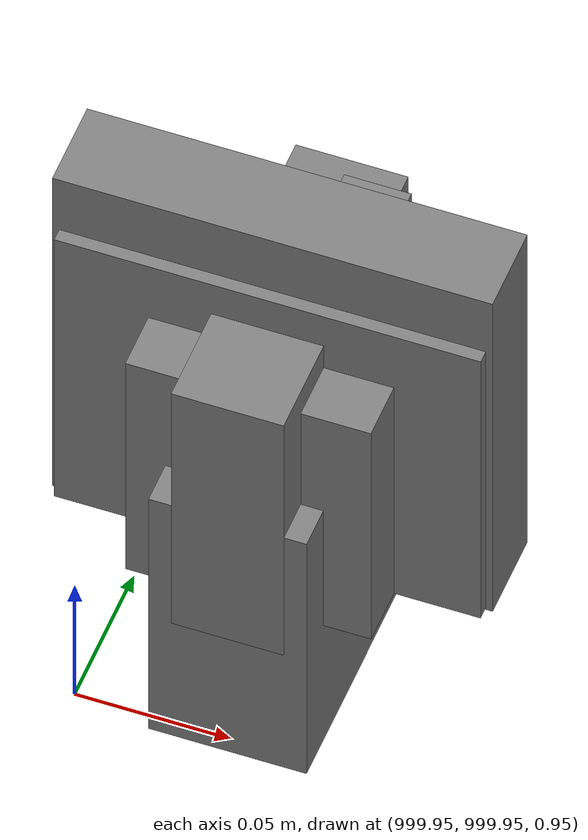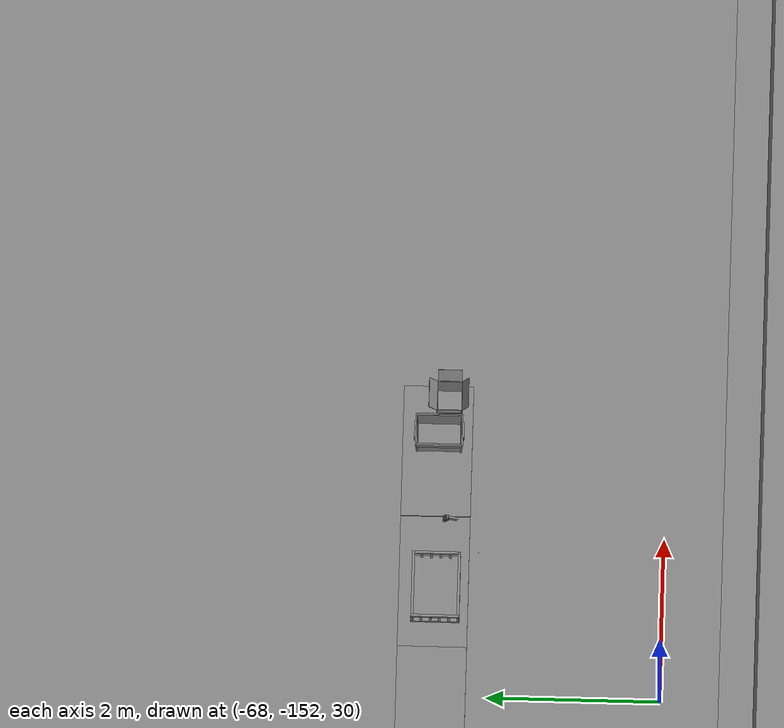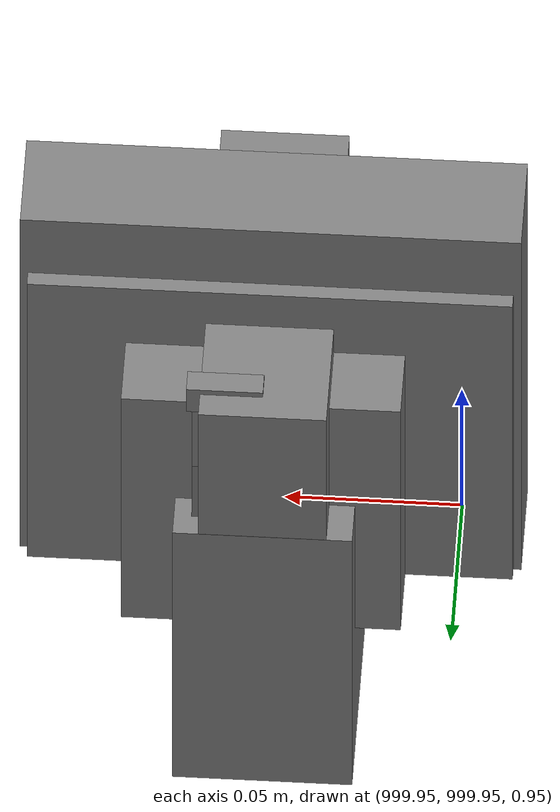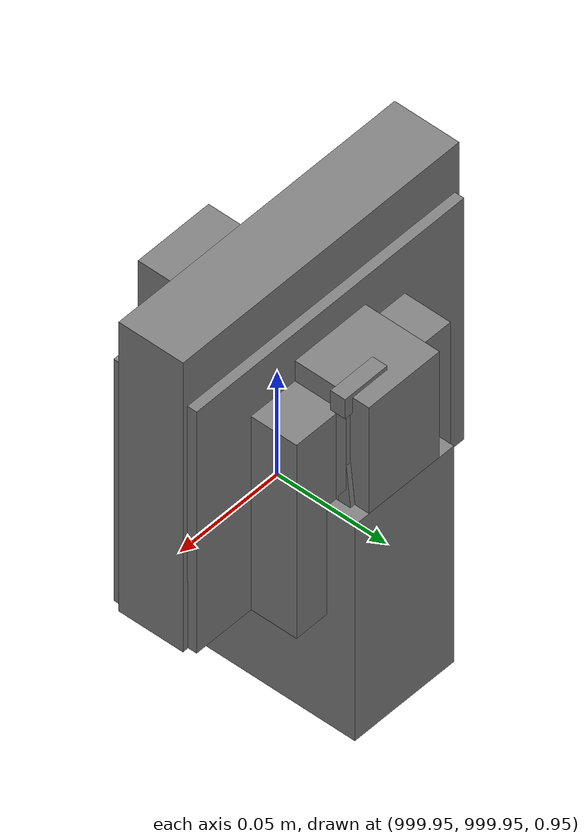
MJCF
<mujoco>
    <option gravity="0.000000000 0.000000000 -9.810000420" timestep="0.0049999999" integrator="implicitfast" density="1.225" viscosity="1.8000001e-05" noslip_iterations="10" iterations="100" sdf_iterations="50">
        <flag multiccd="disable"/>
    </option>
    <size memory="1000M"/>
    <compiler coordinate="local"/>
    <worldbody>
        <light cutoff="30" pos="0 1 1" dir="0 -1 -2"/>
        <light cutoff="30" pos="0 -1 1" dir="0 1 -2"/>
        <body pos="-64.866622925 -149.383972168 30.183746338" euler="89.999984741 89.999946594 0.000000000" name="openloong_gripper_2f85_fix_base_usda_bluebox_01">
            <geom contype="1" conaffinity="1" density="1000" type="box" material="" rgba="0.500000000 0.500000000 0.500000000 1.000000000" solimp="0.899999976 0.949999988 0.001000000" friction="1.000000000 0.005000000 0.000100000" solref="0.020000000 1.000000000" margin="0" condim="3" group="0" pos="0.276580811 0.187225342 0.000068665" quat="0.707106948 0.000077471 0.707106352 0.000077486" size="0.100000001 0.057999998 0.010000000" name="openloong_gripper_2f85_fix_base_usda_geom_38A9D7D1_C6A6_49F2_B82F_612CFD1FB97A"/>
            <geom contype="1" conaffinity="1" density="1000" type="box" material="" rgba="0.500000000 0.500000000 0.500000000 1.000000000" solimp="0.899999976 0.949999988 0.001000000" friction="1.000000000 0.005000000 0.000100000" solref="0.020000000 1.000000000" margin="0" condim="3" group="0" pos="0.000000000 0.002883911 0.000000000" quat="0.999999881 0.000000000 0.000000000 0.000000000" size="0.254000008 0.003000000 0.172000006" name="openloong_gripper_2f85_fix_base_usda_geom_52CF21A9_C374_4FD5_869F_0B18552B1D54"/>
            <geom contype="1" conaffinity="1" density="1000" type="box" material="" rgba="0.500000000 0.500000000 0.500000000 1.000000000" solimp="0.899999976 0.949999988 0.001000000" friction="1.000000000 0.005000000 0.000100000" solref="0.020000000 1.000000000" margin="0" condim="3" group="0" pos="0.000000000 0.124874115 0.173484802" quat="0.999796331 0.020176515 -0.000000015 0.000000030" size="0.259999990 0.119999997 0.007000000" name="openloong_gripper_2f85_fix_base_usda_geom_3BDED38C_346C_4D6E_A03D_8F6C60279588"/>
            <geom contype="1" conaffinity="1" density="1000" type="box" material="" rgba="0.500000000 0.500000000 0.500000000 1.000000000" solimp="0.899999976 0.949999988 0.001000000" friction="1.000000000 0.005000000 0.000100000" solref="0.020000000 1.000000000" margin="0" condim="3" group="0" pos="0.000000000 0.124874115 -0.173469543" quat="0.999796331 -0.020176545 -0.000000015 0.000000000" size="0.259999990 0.119999997 0.007000000" name="openloong_gripper_2f85_fix_base_usda_geom_14E76F63_FE72_4FCB_AD8B_2A0B6A2CB665"/>
            <geom contype="1" conaffinity="1" density="1000" type="box" material="" rgba="0.500000000 0.500000000 0.500000000 1.000000000" solimp="0.899999976 0.949999988 0.001000000" friction="1.000000000 0.005000000 0.000100000" solref="0.020000000 1.000000000" margin="0" condim="3" group="0" pos="0.000000000 0.214008331 0.188980103" quat="0.999912977 0.013176724 0.000000015 0.000000000" size="0.259999990 0.029999999 0.012500000" name="openloong_gripper_2f85_fix_base_usda_geom_4033E9B4_2CD2_4EBC_BB79_862B67FDCAAA"/>
            <geom contype="1" conaffinity="1" density="1000" type="box" material="" rgba="0.500000000 0.500000000 0.500000000 1.000000000" solimp="0.899999976 0.949999988 0.001000000" friction="1.000000000 0.005000000 0.000100000" solref="0.020000000 1.000000000" margin="0" condim="3" group="0" pos="-0.258361816 0.125289917 0.001876831" quat="0.702796936 -0.020792112 0.710783124 0.020769298" size="0.189999998 0.119999997 0.009000000" name="openloong_gripper_2f85_fix_base_usda_geom_7ACC3D99_B823_4C2E_9A65_5FD36D167E2D"/>
            <geom contype="1" conaffinity="1" density="1000" type="box" material="" rgba="0.500000000 0.500000000 0.500000000 1.000000000" solimp="0.899999976 0.949999988 0.001000000" friction="1.000000000 0.005000000 0.000100000" solref="0.020000000 1.000000000" margin="0" condim="3" group="0" pos="0.000000000 0.214008331 -0.188980103" quat="0.999912977 -0.013176769 0.000000030 0.000000015" size="0.259999990 0.029999999 0.012500000" name="openloong_gripper_2f85_fix_base_usda_geom_977E135B_F2CD_4204_9EE3_0467CBF64F17"/>
            <geom contype="1" conaffinity="1" density="1000" type="box" material="" rgba="0.500000000 0.500000000 0.500000000 1.000000000" solimp="0.899999976 0.949999988 0.001000000" friction="1.000000000 0.005000000 0.000100000" solref="0.020000000 1.000000000" margin="0" condim="3" group="0" pos="-0.276611328 0.187225342 0.000068665" quat="0.707106650 0.000077441 0.707106709 0.000077456" size="0.100000001 0.057999998 0.010000000" name="openloong_gripper_2f85_fix_base_usda_geom_4C542B48_B023_4E22_8B4C_E081348D059E"/>
            <geom contype="1" conaffinity="1" density="1000" type="box" material="" rgba="0.500000000 0.500000000 0.500000000 1.000000000" solimp="0.899999976 0.949999988 0.001000000" friction="1.000000000 0.005000000 0.000100000" solref="0.020000000 1.000000000" margin="0" condim="3" group="0" pos="0.258331299 0.125289917 0.001876831" quat="0.702851415 0.018856421 0.710823774 -0.019329369" size="0.189999998 0.119999997 0.009000000" name="openloong_gripper_2f85_fix_base_usda_geom_4BE02CBD_BBAE_4760_9D24_92D5D9669355"/>
            <freejoint name="openloong_gripper_2f85_fix_base_usda_bluebox_01_joint"/>
            <site size="0.005000000 0.005000000 0.005000000" rgba="0.500000000 0.500000000 0.500000000 1.000000000" pos="0.000000000 0.000000000 0.000000000" quat="0.999961913 0.008726534 0.000000000 0.000000000" group="0" type="sphere" name="openloong_gripper_2f85_fix_base_usda_bluebox_01site"/>
        </body>
        <body pos="-64.496299744 -149.491867065 30.235729218" euler="0.000000000 0.000000000 89.999946594" name="openloong_gripper_2f85_fix_base_usda_cardboardbox_01">
            <geom contype="1" conaffinity="1" density="1000" type="box" material="" rgba="0.500000000 0.500000000 0.500000000 1.000000000" solimp="0.899999976 0.949999988 0.001000000" friction="1.000000000 0.005000000 0.000100000" solref="0.020000000 1.000000000" margin="0" condim="3" group="0" pos="-0.003166199 -0.004086494 0.005052090" quat="1.000000000 0.000000000 0.000000000 0.000000000" size="0.142499998 0.177500010 0.005000000" name="openloong_gripper_2f85_fix_base_usda_geom_E1D581B5_BCD1_48D4_AB59_179189876686"/>
            <geom contype="1" conaffinity="1" density="1000" type="box" material="" rgba="0.500000000 0.500000000 0.500000000 1.000000000" solimp="0.899999976 0.949999988 0.001000000" friction="1.000000000 0.005000000 0.000100000" solref="0.020000000 1.000000000" margin="0" condim="3" group="0" pos="-0.003166199 0.170316696 0.150570869" quat="1.000000000 0.000000000 0.000000000 0.000000000" size="0.142499998 0.005000000 0.149999991" name="openloong_gripper_2f85_fix_base_usda_geom_8F6BD664_CAA4_4A0E_952C_79C51D9765F1"/>
            <geom contype="1" conaffinity="1" density="1000" type="box" material="" rgba="0.500000000 0.500000000 0.500000000 1.000000000" solimp="0.899999976 0.949999988 0.001000000" friction="1.000000000 0.005000000 0.000100000" solref="0.020000000 1.000000000" margin="0" condim="3" group="0" pos="-0.147399902 -0.005307198 0.150570869" quat="1.000000000 0.000000000 0.000000000 0.000000000" size="0.005000000 0.177500010 0.149999991" name="openloong_gripper_2f85_fix_base_usda_geom_AAC2DBB7_94A9_4D23_BB6E_2072766A7C31"/>
            <geom contype="1" conaffinity="1" density="1000" type="box" material="" rgba="0.500000000 0.500000000 0.500000000 1.000000000" solimp="0.899999976 0.949999988 0.001000000" friction="1.000000000 0.005000000 0.000100000" solref="0.020000000 1.000000000" margin="0" condim="3" group="0" pos="0.140275955 -0.005307198 0.150570869" quat="1.000000000 0.000000000 0.000000000 0.000000000" size="0.005000000 0.177500010 0.149999991" name="openloong_gripper_2f85_fix_base_usda_geom_FD3A8C45_5454_4F18_81DD_39FD023CC365"/>
            <geom contype="1" conaffinity="1" density="1000" type="box" material="" rgba="0.500000000 0.500000000 0.500000000 1.000000000" solimp="0.899999976 0.949999988 0.001000000" friction="1.000000000 0.005000000 0.000100000" solref="0.020000000 1.000000000" margin="0" condim="3" group="0" pos="-0.003166199 -0.181550980 0.150570869" quat="1.000000000 0.000000000 0.000000000 0.000000000" size="0.142499998 0.005000000 0.149999991" name="openloong_gripper_2f85_fix_base_usda_geom_DD777E74_3BAC_47B5_85E8_36A783748001"/>
            <freejoint name="openloong_gripper_2f85_fix_base_usda_cardboardbox_01_joint"/>
            <site size="0.005000000 0.005000000 0.005000000" rgba="0.500000000 0.500000000 0.500000000 1.000000000" pos="0.000000000 0.000000000 0.000000000" quat="0.999961913 0.008726535 0.000000000 0.000000000" group="0" type="sphere" name="openloong_gripper_2f85_fix_base_usda_site_E2C21F3A_2435_4A99_B5C5_978206D94145"/>
            <body pos="0.139160156 -0.004048347 0.301930904" euler="-179.999954224 49.383502960 179.999954224" name="openloong_gripper_2f85_fix_base_usda_A1_006">
                <geom contype="1" conaffinity="1" density="1000" type="box" material="" rgba="0.500000000 0.500000000 0.500000000 1.000000000" solimp="0.899999976 0.949999988 0.001000000" friction="1.000000000 0.005000000 0.000100000" solref="0.020000000 1.000000000" margin="0" condim="3" group="0" pos="-0.071587563 0.000009537 0.001745224" quat="0.999999881 0.000000000 0.000000000 0.000000000" size="0.071249999 0.179999992 0.002500000" name="openloong_gripper_2f85_fix_base_usda_geom_18FE404C_03B1_4C64_8C56_8E7048D8CFED"/>
                <joint armature="0" stiffness="0.07" damping="0.0099999998" axis="0.000000 1.000000 0.000000" type="hinge" name="openloong_gripper_2f85_fix_base_usda_A1_006"/>
            </body>
            <body pos="-0.145902634 -0.004086494 0.301938057" euler="-180.000000000 -60.000011444 -180.000000000" name="openloong_gripper_2f85_fix_base_usda_A2_006">
                <geom contype="1" conaffinity="1" density="1000" type="box" material="" rgba="0.500000000 0.500000000 0.500000000 1.000000000" solimp="0.899999976 0.949999988 0.001000000" friction="1.000000000 0.005000000 0.000100000" solref="0.020000000 1.000000000" margin="0" condim="3" group="0" pos="0.071268082 0.000009537 0.002717972" quat="0.000002921 0.000000000 -0.000000030 0.999999881" size="0.071249999 0.179999992 0.002500000" name="openloong_gripper_2f85_fix_base_usda_geom_9029974C_F6FF_4542_9EF9_CF61FF6CAAFF"/>
                <joint armature="0" stiffness="0.07" damping="0.0099999998" axis="0.000000 1.000000 0.000000" type="hinge" name="openloong_gripper_2f85_fix_base_usda_A2_006"/>
            </body>
            <body pos="-0.003385544 0.175991058 0.301930904" euler="-125.858116150 -0.000004561 0.000002331" name="openloong_gripper_2f85_fix_base_usda_B2_006">
                <geom contype="1" conaffinity="1" density="1000" type="box" material="" rgba="0.500000000 0.500000000 0.500000000 1.000000000" solimp="0.899999976 0.949999988 0.001000000" friction="1.000000000 0.005000000 0.000100000" solref="0.020000000 1.000000000" margin="0" condim="3" group="0" pos="0.000009537 -0.070939064 -0.002470016" quat="0.999614120 0.027776197 -0.000000015 0.000000030" size="0.137500003 0.064999998 0.005000000" name="openloong_gripper_2f85_fix_base_usda_geom_C64FFBBC_20C5_4DB0_A941_52F1CFF7C5ED"/>
                <joint armature="0" stiffness="0.07" damping="0.0099999998" axis="1.000000 0.000000 0.000000" type="hinge" name="openloong_gripper_2f85_fix_base_usda_B2_006"/>
            </body>
            <body pos="-0.003385544 -0.184140205 0.301938057" euler="147.805557251 0.000000000 0.000000000" name="openloong_gripper_2f85_fix_base_usda_B1_006">
                <geom contype="1" conaffinity="1" density="1000" type="box" material="" rgba="0.500000000 0.500000000 0.500000000 1.000000000" solimp="0.899999976 0.949999988 0.001000000" friction="1.000000000 0.005000000 0.000100000" solref="0.020000000 1.000000000" margin="0" condim="3" group="0" pos="-0.000028610 0.070202351 -0.002703667" quat="0.999614179 -0.027776167 0.000000000 0.000000000" size="0.137500003 0.064999998 0.005000000" name="openloong_gripper_2f85_fix_base_usda_geom_334C3F47_9593_4C2D_B3B1_8A8C044216E0"/>
                <joint armature="0" stiffness="0.07" damping="0.0099999998" axis="1.000000 0.000000 0.000000" type="hinge" name="openloong_gripper_2f85_fix_base_usda_B1_006"/>
            </body>
        </body>
        <body pos="-65.882858276 -149.481979370 30.229999542" euler="-64.487716675 0.000000000 0.000000000" name="openloong_gripper_2f85_fix_base_usda_Barcode">
            <geom contype="1" conaffinity="1" density="1000" type="box" material="" rgba="0.500000000 0.500000000 0.500000000 1.000000000" solimp="0.899999976 0.949999988 0.001000000" friction="1.000000000 0.005000000 0.000100000" solref="0.020000000 1.000000000" margin="0" condim="3" group="0" pos="0.000000000 0.013038635 0.001419067" quat="0.000000000 0.000000000 0.000000000 1.000000119" size="0.034000002 0.010000000 0.017999999" name="openloong_gripper_2f85_fix_base_usda_geom_BC32A8FC_8DE3_4705_85E9_0ACC8A1CCDF8"/>
            <geom contype="1" conaffinity="1" density="1000" type="box" material="" rgba="0.500000000 0.500000000 0.500000000 1.000000000" solimp="0.899999976 0.949999988 0.001000000" friction="1.000000000 0.005000000 0.000100000" solref="0.020000000 1.000000000" margin="0" condim="3" group="0" pos="0.000000000 -0.035301208 -0.007095337" quat="0.000000000 0.000000000 -0.043619365 0.999048233" size="0.028999999 0.010000000 0.020000000" name="openloong_gripper_2f85_fix_base_usda_geom_CA780E77_1EB5_48C1_96F3_3090CAAB43C0"/>
            <geom contype="1" conaffinity="1" density="1000" type="box" material="" rgba="0.500000000 0.500000000 0.500000000 1.000000000" solimp="0.899999976 0.949999988 0.001000000" friction="1.000000000 0.005000000 0.000100000" solref="0.020000000 1.000000000" margin="0" condim="3" group="0" pos="0.000000000 -0.043411255 -0.011749268" quat="0.922262907 0.386563420 0.000000000 0.000000000" size="0.026000001 0.010000000 0.020000000" name="openloong_gripper_2f85_fix_base_usda_geom_25030FB1_BD0D_4A3B_AC51_B913F773E01B"/>
            <geom contype="1" conaffinity="1" density="1000" type="box" material="" rgba="0.500000000 0.500000000 0.500000000 1.000000000" solimp="0.899999976 0.949999988 0.001000000" friction="1.000000000 0.005000000 0.000100000" solref="0.020000000 1.000000000" margin="0" condim="3" group="0" pos="0.000000000 -0.016967773 -0.031860352" quat="0.000000000 0.000000000 0.000000000 1.000000119" size="0.008000000 0.010000000 0.013000000" name="openloong_gripper_2f85_fix_base_usda_geom_EEBC291B_6964_45F4_89B6_15DAAC4748FE"/>
            <geom contype="1" conaffinity="1" density="1000" type="box" material="" rgba="0.500000000 0.500000000 0.500000000 1.000000000" solimp="0.899999976 0.949999988 0.001000000" friction="1.000000000 0.005000000 0.000100000" solref="0.020000000 1.000000000" margin="0" condim="3" group="0" pos="0.000000000 -0.001869202 0.000312805" quat="0.953716993 0.300705761 0.000000000 0.000000000" size="0.032000002 0.010000000 0.018999999" name="openloong_gripper_2f85_fix_base_usda_geom_62D07C5C_8AAA_4830_AFB8_BB91DA556CFD"/>
            <geom contype="1" conaffinity="1" density="1000" type="box" material="" rgba="0.500000000 0.500000000 0.500000000 1.000000000" solimp="0.899999976 0.949999988 0.001000000" friction="1.000000000 0.005000000 0.000100000" solref="0.020000000 1.000000000" margin="0" condim="3" group="0" pos="0.000000000 -0.019531250 -0.003173828" quat="0.953716993 0.300705761 0.000000000 0.000000000" size="0.030999999 0.010000000 0.020000000" name="openloong_gripper_2f85_fix_base_usda_geom_8BD07B1F_2553_4456_9A8C_A92636D12CCC"/>
            <geom contype="1" conaffinity="1" density="1000" type="box" material="" rgba="0.500000000 0.500000000 0.500000000 1.000000000" solimp="0.899999976 0.949999988 0.001000000" friction="1.000000000 0.005000000 0.000100000" solref="0.020000000 1.000000000" margin="0" condim="3" group="0" pos="0.000000000 -0.035301208 -0.007095337" quat="0.953716993 0.300705761 0.000000000 0.000000000" size="0.028999999 0.010000000 0.020000000" name="openloong_gripper_2f85_fix_base_usda_geom_43301B1C_5F6A_4A01_855A_B1EDEC738FAB"/>
            <geom contype="1" conaffinity="1" density="1000" type="box" material="" rgba="0.500000000 0.500000000 0.500000000 1.000000000" solimp="0.899999976 0.949999988 0.001000000" friction="1.000000000 0.005000000 0.000100000" solref="0.020000000 1.000000000" margin="0" condim="3" group="0" pos="0.000000000 -0.042617798 -0.071121216" quat="0.000000000 0.000000000 0.000000000 1.000000119" size="0.013000000 0.021000000 0.059999999" name="openloong_gripper_2f85_fix_base_usda_geom_831BFDCD_563D_4BFD_890F_8F27313B4F9A"/>
            <freejoint name="openloong_gripper_2f85_fix_base_usda_Barcode_joint"/>
            <site size="0.005000000 0.005000000 0.005000000" rgba="0.500000000 0.500000000 0.500000000 1.000000000" pos="0.000000000 0.000000000 0.000000000" quat="1.000000000 0.000000000 0.000000000 0.000000000" group="0" type="sphere" name="openloong_gripper_2f85_fix_base_usda_Barcode_site"/>
        </body>
        <body pos="-66.745018005 -149.392349243 30.184000015" euler="0.000000000 0.000000000 89.999946594" name="[22330232128377]_Basket_01">
            <geom contype="1" conaffinity="1" density="1000" type="box" material="" rgba="0.500000000 0.500000000 0.500000000 1.000000000" solimp="0.899999976 0.949999988 0.001000000" friction="1.000000000 0.005000000 0.000100000" solref="0.020000000 1.000000000" margin="0" condim="3" group="0" pos="-0.052425385 0.389207840 0.089787483" quat="0.707107008 0.000000000 0.000000000 0.707106411" size="0.014249999 0.014249999 0.059999999" name="[22330232128377]_geom_3E2E76AE_5658_47FB_80D6_13430C581A21"/>
            <geom contype="1" conaffinity="1" density="1000" type="box" material="" rgba="0.500000000 0.500000000 0.500000000 1.000000000" solimp="0.899999976 0.949999988 0.001000000" friction="1.000000000 0.005000000 0.000100000" solref="0.020000000 1.000000000" margin="0" condim="3" group="0" pos="0.264015198 -0.133043289 0.089787483" quat="0.707107008 0.000000000 0.000000000 0.707106411" size="0.014249999 0.014249999 0.059999999" name="[22330232128377]_geom_56C085B8_D254_49DE_AC1E_232C3E455876"/>
            <geom contype="1" conaffinity="1" density="1000" type="box" material="" rgba="0.500000000 0.500000000 0.500000000 1.000000000" solimp="0.899999976 0.949999988 0.001000000" friction="1.000000000 0.005000000 0.000100000" solref="0.020000000 1.000000000" margin="0" condim="3" group="0" pos="-0.264015198 -0.265548706 0.089793205" quat="0.707107008 0.000000000 0.000000000 0.707106411" size="0.014249999 0.014249999 0.059999999" name="[22330232128377]_geom_3BFEE97A_8111_4759_A435_D042447D2491"/>
            <geom contype="1" conaffinity="1" density="1000" type="box" material="" rgba="0.500000000 0.500000000 0.500000000 1.000000000" solimp="0.899999976 0.949999988 0.001000000" friction="1.000000000 0.005000000 0.000100000" solref="0.020000000 1.000000000" margin="0" condim="3" group="0" pos="-0.160263062 -0.389322281 0.089793205" quat="0.707107008 0.000000000 0.000000000 0.707106411" size="0.014249999 0.014249999 0.059999999" name="[22330232128377]_geom_036E8B6B_0CAA_415B_A808_37152CA0FEFB"/>
            <geom contype="1" conaffinity="1" density="1000" type="box" material="" rgba="0.500000000 0.500000000 0.500000000 1.000000000" solimp="0.899999976 0.949999988 0.001000000" friction="1.000000000 0.005000000 0.000100000" solref="0.020000000 1.000000000" margin="0" condim="3" group="0" pos="0.162265778 -0.389322281 0.089787483" quat="0.707107008 0.000000000 0.000000000 0.707106411" size="0.014249999 0.014249999 0.059999999" name="[22330232128377]_geom_FF186930_0B7F_4AA5_83ED_6C3BB9872CF5"/>
            <geom contype="1" conaffinity="1" density="1000" type="box" material="" rgba="0.500000000 0.500000000 0.500000000 1.000000000" solimp="0.899999976 0.949999988 0.001000000" friction="1.000000000 0.005000000 0.000100000" solref="0.020000000 1.000000000" margin="0" condim="3" group="0" pos="0.264015198 0.389207840 0.089787483" quat="0.707107008 0.000000000 0.000000000 0.707106411" size="0.014249999 0.014249999 0.059999999" name="[22330232128377]_geom_02ABC40D_A73C_4678_81F5_3376CF4BAF09"/>
            <geom contype="1" conaffinity="1" density="1000" type="box" material="" rgba="0.500000000 0.500000000 0.500000000 1.000000000" solimp="0.899999976 0.949999988 0.001000000" friction="1.000000000 0.005000000 0.000100000" solref="0.020000000 1.000000000" margin="0" condim="3" group="0" pos="-0.264015198 -0.133043289 0.089793205" quat="0.707107008 0.000000000 0.000000000 0.707106411" size="0.014249999 0.014249999 0.059999999" name="[22330232128377]_geom_D7762E8C_7473_4505_AC59_A45123C6DE76"/>
            <geom contype="1" conaffinity="1" density="1000" type="box" material="" rgba="0.500000000 0.500000000 0.500000000 1.000000000" solimp="0.899999976 0.949999988 0.001000000" friction="1.000000000 0.005000000 0.000100000" solref="0.020000000 1.000000000" margin="0" condim="3" group="0" pos="-0.264026642 0.269256592 0.089793205" quat="0.707107008 0.000000000 0.000000000 0.707106411" size="0.014249999 0.014249999 0.059999999" name="[22330232128377]_geom_238D8A50_3E7A_4114_BDCB_7FAF96CB58C8"/>
            <geom contype="1" conaffinity="1" density="1000" type="box" material="" rgba="0.500000000 0.500000000 0.500000000 1.000000000" solimp="0.899999976 0.949999988 0.001000000" friction="1.000000000 0.005000000 0.000100000" solref="0.020000000 1.000000000" margin="0" condim="3" group="0" pos="0.054462433 0.389207840 0.089787483" quat="0.707107008 0.000000000 0.000000000 0.707106411" size="0.014249999 0.014249999 0.059999999" name="[22330232128377]_geom_A233FDA4_F78F_451A_A6C2_208E20CEE302"/>
            <geom contype="1" conaffinity="1" density="1000" type="box" material="" rgba="0.500000000 0.500000000 0.500000000 1.000000000" solimp="0.899999976 0.949999988 0.001000000" friction="1.000000000 0.005000000 0.000100000" solref="0.020000000 1.000000000" margin="0" condim="3" group="0" pos="0.054462433 -0.389322281 0.089787483" quat="0.707107008 0.000000000 0.000000000 0.707106411" size="0.014249999 0.014249999 0.059999999" name="[22330232128377]_geom_616C1705_DC98_4553_A3B8_FB52BF5EC17A"/>
            <geom contype="1" conaffinity="1" density="1000" type="box" material="" rgba="0.500000000 0.500000000 0.500000000 1.000000000" solimp="0.899999976 0.949999988 0.001000000" friction="1.000000000 0.005000000 0.000100000" solref="0.020000000 1.000000000" margin="0" condim="3" group="0" pos="0.264015198 0.269256592 0.089793205" quat="0.707107008 0.000000000 0.000000000 0.707106411" size="0.014249999 0.014249999 0.059999999" name="[22330232128377]_geom_C1B47A4D_8F9B_49F2_895F_4A3930E0F2BE"/>
            <geom contype="1" conaffinity="1" density="1000" type="box" material="" rgba="0.500000000 0.500000000 0.500000000 1.000000000" solimp="0.899999976 0.949999988 0.001000000" friction="1.000000000 0.005000000 0.000100000" solref="0.020000000 1.000000000" margin="0" condim="3" group="0" pos="0.264015198 -0.389322281 0.089787483" quat="0.707107008 0.000000000 0.000000000 0.707106411" size="0.014249999 0.014249999 0.059999999" name="[22330232128377]_geom_8993D86F_CA4A_43D7_BC6C_948C07662279"/>
            <geom contype="1" conaffinity="1" density="1000" type="box" material="" rgba="0.500000000 0.500000000 0.500000000 1.000000000" solimp="0.899999976 0.949999988 0.001000000" friction="1.000000000 0.005000000 0.000100000" solref="0.020000000 1.000000000" margin="0" condim="3" group="0" pos="0.000000000 0.000000000 0.015998840" quat="0.707107008 0.000000000 0.000000000 0.707106411" size="0.403499991 0.279000014 0.015750000" name="[22330232128377]_geom_950A6FDD_ABAB_4F7A_A63F_3C235F3DCF10"/>
            <geom contype="1" conaffinity="1" density="1000" type="box" material="" rgba="0.500000000 0.500000000 0.500000000 1.000000000" solimp="0.899999976 0.949999988 0.001000000" friction="1.000000000 0.005000000 0.000100000" solref="0.020000000 1.000000000" margin="0" condim="3" group="0" pos="0.000000000 -0.389476776 0.163619041" quat="0.707107008 0.000000000 0.000000000 0.707106411" size="0.015000000 0.277500004 0.015750000" name="[22330232128377]_geom_A128E2CF_1BE3_4FB7_8CE3_7F4DE1693CA0"/>
            <geom contype="1" conaffinity="1" density="1000" type="box" material="" rgba="0.500000000 0.500000000 0.500000000 1.000000000" solimp="0.899999976 0.949999988 0.001000000" friction="1.000000000 0.005000000 0.000100000" solref="0.020000000 1.000000000" margin="0" condim="3" group="0" pos="0.162265778 0.389207840 0.089787483" quat="0.707107008 0.000000000 0.000000000 0.707106411" size="0.014249999 0.014249999 0.059999999" name="[22330232128377]_geom_F4FEAA99_A9C1_4831_9326_C45741D7791D"/>
            <geom contype="1" conaffinity="1" density="1000" type="box" material="" rgba="0.500000000 0.500000000 0.500000000 1.000000000" solimp="0.899999976 0.949999988 0.001000000" friction="1.000000000 0.005000000 0.000100000" solref="0.020000000 1.000000000" margin="0" condim="3" group="0" pos="0.000000000 0.389471054 0.163619041" quat="0.707107008 0.000000000 0.000000000 0.707106411" size="0.015000000 0.277500004 0.015750000" name="[22330232128377]_geom_57D80607_66D6_4073_81BD_4EB0860FD1F4"/>
            <geom contype="1" conaffinity="1" density="1000" type="box" material="" rgba="0.500000000 0.500000000 0.500000000 1.000000000" solimp="0.899999976 0.949999988 0.001000000" friction="1.000000000 0.005000000 0.000100000" solref="0.020000000 1.000000000" margin="0" condim="3" group="0" pos="-0.263511658 0.000000000 0.163619041" quat="0.707107008 0.000000000 0.000000000 0.707106411" size="0.403499991 0.015000000 0.015750000" name="[22330232128377]_geom_4DBD2140_2805_4937_88DD_2225ED9897BE"/>
            <geom contype="1" conaffinity="1" density="1000" type="box" material="" rgba="0.500000000 0.500000000 0.500000000 1.000000000" solimp="0.899999976 0.949999988 0.001000000" friction="1.000000000 0.005000000 0.000100000" solref="0.020000000 1.000000000" margin="0" condim="3" group="0" pos="-0.264015198 0.141334534 0.089793205" quat="0.707107008 0.000000000 0.000000000 0.707106411" size="0.014249999 0.014249999 0.059999999" name="[22330232128377]_geom_B274469C_15C1_42EF_9E35_141278AF8098"/>
            <geom contype="1" conaffinity="1" density="1000" type="box" material="" rgba="0.500000000 0.500000000 0.500000000 1.000000000" solimp="0.899999976 0.949999988 0.001000000" friction="1.000000000 0.005000000 0.000100000" solref="0.020000000 1.000000000" margin="0" condim="3" group="0" pos="0.264015198 -0.265548706 0.089787483" quat="0.707107008 0.000000000 0.000000000 0.707106411" size="0.014249999 0.014249999 0.059999999" name="[22330232128377]_geom_0924AB06_6C27_4882_89B9_27BFD679C3B7"/>
            <geom contype="1" conaffinity="1" density="1000" type="box" material="" rgba="0.500000000 0.500000000 0.500000000 1.000000000" solimp="0.899999976 0.949999988 0.001000000" friction="1.000000000 0.005000000 0.000100000" solref="0.020000000 1.000000000" margin="0" condim="3" group="0" pos="-0.160263062 0.389207840 0.089787483" quat="0.707107008 0.000000000 0.000000000 0.707106411" size="0.014249999 0.014249999 0.059999999" name="[22330232128377]_geom_EB449BE2_295E_4D78_A3DF_33DCAC32788F"/>
            <geom contype="1" conaffinity="1" density="1000" type="box" material="" rgba="0.500000000 0.500000000 0.500000000 1.000000000" solimp="0.899999976 0.949999988 0.001000000" friction="1.000000000 0.005000000 0.000100000" solref="0.020000000 1.000000000" margin="0" condim="3" group="0" pos="-0.052425385 -0.389322281 0.089787483" quat="0.707107008 0.000000000 0.000000000 0.707106411" size="0.014249999 0.014249999 0.059999999" name="[22330232128377]_geom_D552EA84_3018_4501_890E_8F7FBB7C28D7"/>
            <geom contype="1" conaffinity="1" density="1000" type="box" material="" rgba="0.500000000 0.500000000 0.500000000 1.000000000" solimp="0.899999976 0.949999988 0.001000000" friction="1.000000000 0.005000000 0.000100000" solref="0.020000000 1.000000000" margin="0" condim="3" group="0" pos="-0.264026642 -0.389322281 0.089793205" quat="0.707107008 0.000000000 0.000000000 0.707106411" size="0.014249999 0.014249999 0.059999999" name="[22330232128377]_geom_F37F50A1_28F5_4CC7_82CD_3718311808F2"/>
            <geom contype="1" conaffinity="1" density="1000" type="box" material="" rgba="0.500000000 0.500000000 0.500000000 1.000000000" solimp="0.899999976 0.949999988 0.001000000" friction="1.000000000 0.005000000 0.000100000" solref="0.020000000 1.000000000" margin="0" condim="3" group="0" pos="0.264015198 0.141334534 0.089787483" quat="0.707107008 0.000000000 0.000000000 0.707106411" size="0.014249999 0.014249999 0.059999999" name="[22330232128377]_geom_94B72871_C11D_4FF0_AAE4_A1AF54D7DB30"/>
            <geom contype="1" conaffinity="1" density="1000" type="box" material="" rgba="0.500000000 0.500000000 0.500000000 1.000000000" solimp="0.899999976 0.949999988 0.001000000" friction="1.000000000 0.005000000 0.000100000" solref="0.020000000 1.000000000" margin="0" condim="3" group="0" pos="-0.264015198 0.389207840 0.089793205" quat="0.707107008 0.000000000 0.000000000 0.707106411" size="0.014249999 0.014249999 0.059999999" name="[22330232128377]_geom_084809ED_4121_4095_BFF3_B849F284EFC7"/>
            <geom contype="1" conaffinity="1" density="1000" type="box" material="" rgba="0.500000000 0.500000000 0.500000000 1.000000000" solimp="0.899999976 0.949999988 0.001000000" friction="1.000000000 0.005000000 0.000100000" solref="0.020000000 1.000000000" margin="0" condim="3" group="0" pos="0.264015198 0.004480362 0.089787483" quat="0.707107008 0.000000000 0.000000000 0.707106411" size="0.014249999 0.014249999 0.059999999" name="[22330232128377]_geom_BDB2CD8E_476A_4D2B_A42F_B3EB6EB22EC7"/>
            <geom contype="1" conaffinity="1" density="1000" type="box" material="" rgba="0.500000000 0.500000000 0.500000000 1.000000000" solimp="0.899999976 0.949999988 0.001000000" friction="1.000000000 0.005000000 0.000100000" solref="0.020000000 1.000000000" margin="0" condim="3" group="0" pos="0.263694763 -0.000011444 0.163619041" quat="0.707107008 0.000000000 0.000000000 0.707106411" size="0.403499991 0.015000000 0.015750000" name="[22330232128377]_geom_C9D03345_E331_495D_A2B5_AE56BDCCF317"/>
            <geom contype="1" conaffinity="1" density="1000" type="box" material="" rgba="0.500000000 0.500000000 0.500000000 1.000000000" solimp="0.899999976 0.949999988 0.001000000" friction="1.000000000 0.005000000 0.000100000" solref="0.020000000 1.000000000" margin="0" condim="3" group="0" pos="-0.264015198 0.004480362 0.089793205" quat="0.707107008 0.000000000 0.000000000 0.707106411" size="0.014249999 0.014249999 0.059999999" name="[22330232128377]_geom_CEAEFF66_6EB1_4F15_A31B_262454AF9A8A"/>
            <freejoint name="[22330232128377]_joint_1FA97E26_7EBA_4915_8ABD_E66D4BAF782F"/>
        </body>
        <body pos="0.000000000 0.000000000 0.000000000" euler="0.000000000 0.000000000 0.000000000" name="Static Objects_Static Objects">
            <geom contype="1" conaffinity="1" density="1000" type="box" material="" rgba="0.500000000 0.500000000 0.500000000 1.000000000" solimp="0.899999976 0.949999988 0.001000000" friction="1.000000000 0.005000000 0.000100000" solref="0.020000000 1.000000000" margin="0" condim="3" group="0" pos="-67.544113159 -149.365814209 29.727830887" quat="0.500000417 0.499999970 0.499999553 0.499999970" size="0.381000012 0.319999993 0.041000001" name="Static Objects_geom_201CED19_B09F_4E7B_A7C4_141B4F372D15"/>
            <geom contype="1" conaffinity="1" density="1000" type="box" material="" rgba="0.500000000 0.500000000 0.500000000 1.000000000" solimp="0.899999976 0.949999988 0.001000000" friction="1.000000000 0.005000000 0.000100000" solref="0.020000000 1.000000000" margin="0" condim="3" group="0" pos="-68.239501953 -149.365814209 30.086868286" quat="0.500000417 0.499999970 0.499999553 0.499999970" size="0.370999992 0.039500002 0.745000005" name="Static Objects_geom_64FB29A9_C178_49CC_8136_634598CF6DC4"/>
            <geom contype="1" conaffinity="1" density="1000" type="box" material="" rgba="0.500000000 0.500000000 0.500000000 1.000000000" solimp="0.899999976 0.949999988 0.001000000" friction="1.000000000 0.005000000 0.000100000" solref="0.020000000 1.000000000" margin="0" condim="3" group="0" pos="-68.239501953 -149.365814209 30.147235870" quat="0.500000417 0.499999970 0.499999553 0.499999970" size="0.400000006 0.022000000 0.800000012" name="Static Objects_geom_8EE0F2A7_6EDA_4185_98CC_B6BA549AF167"/>
            <geom contype="1" conaffinity="1" density="1000" type="box" material="" rgba="0.500000000 0.500000000 0.500000000 1.000000000" solimp="0.899999976 0.949999988 0.001000000" friction="1.000000000 0.005000000 0.000100000" solref="0.020000000 1.000000000" margin="0" condim="3" group="0" pos="-68.934890747 -149.365814209 29.727830887" quat="0.500000417 0.499999970 0.499999553 0.499999970" size="0.381000012 0.319999993 0.041000001" name="Static Objects_geom_A1C1C11B_5D63_488A_A674_8A94E1926017"/>
            <geom contype="1" conaffinity="1" density="1000" type="box" material="" rgba="0.500000000 0.500000000 0.500000000 1.000000000" solimp="0.899999976 0.949999988 0.001000000" friction="1.000000000 0.005000000 0.000100000" solref="0.020000000 1.000000000" margin="0" condim="3" group="0" pos="-68.239501953 -149.365814209 29.561563492" quat="0.500000417 0.499999970 0.499999553 0.499999970" size="0.020000000 0.022000000 0.660000026" name="Static Objects_geom_EAB5098E_2FBB_4C64_8F65_67310B5FE544"/>
            <geom contype="1" conaffinity="1" density="1000" type="box" material="" rgba="0.500000000 0.500000000 0.500000000 1.000000000" solimp="0.899999976 0.949999988 0.001000000" friction="1.000000000 0.005000000 0.000100000" solref="0.020000000 1.000000000" margin="0" condim="3" group="0" pos="-65.945671082 -149.365814209 29.727830887" quat="0.500000417 0.499999970 0.499999553 0.499999970" size="0.381000012 0.319999993 0.041000001" name="Static Objects_geom_4B11E6BA_B4D3_443E_AADA_C42902D9787A"/>
            <geom contype="1" conaffinity="1" density="1000" type="box" material="" rgba="0.500000000 0.500000000 0.500000000 1.000000000" solimp="0.899999976 0.949999988 0.001000000" friction="1.000000000 0.005000000 0.000100000" solref="0.020000000 1.000000000" margin="0" condim="3" group="0" pos="-66.641059875 -149.365814209 30.086868286" quat="0.500000417 0.499999970 0.499999553 0.499999970" size="0.370999992 0.039500002 0.745000005" name="Static Objects_geom_CA68AE7A_F903_485F_9672_767BCA10DCAB"/>
            <geom contype="1" conaffinity="1" density="1000" type="box" material="" rgba="0.500000000 0.500000000 0.500000000 1.000000000" solimp="0.899999976 0.949999988 0.001000000" friction="1.000000000 0.005000000 0.000100000" solref="0.020000000 1.000000000" margin="0" condim="3" group="0" pos="-66.641059875 -149.365814209 30.147235870" quat="0.500000417 0.499999970 0.499999553 0.499999970" size="0.400000006 0.022000000 0.800000012" name="Static Objects_geom_B8A57692_D109_4E53_8CC8_00C0AAA08D38"/>
            <geom contype="1" conaffinity="1" density="1000" type="box" material="" rgba="0.500000000 0.500000000 0.500000000 1.000000000" solimp="0.899999976 0.949999988 0.001000000" friction="1.000000000 0.005000000 0.000100000" solref="0.020000000 1.000000000" margin="0" condim="3" group="0" pos="-67.336448669 -149.365814209 29.727830887" quat="0.500000417 0.499999970 0.499999553 0.499999970" size="0.381000012 0.319999993 0.041000001" name="Static Objects_geom_64DF70D9_4B06_4D32_9347_575884310816"/>
            <geom contype="1" conaffinity="1" density="1000" type="box" material="" rgba="0.500000000 0.500000000 0.500000000 1.000000000" solimp="0.899999976 0.949999988 0.001000000" friction="1.000000000 0.005000000 0.000100000" solref="0.020000000 1.000000000" margin="0" condim="3" group="0" pos="-66.641059875 -149.365814209 29.561563492" quat="0.500000417 0.499999970 0.499999553 0.499999970" size="0.020000000 0.022000000 0.660000026" name="Static Objects_geom_0F127408_86FF_4CCD_B804_AFCDE09D03B9"/>
            <geom contype="1" conaffinity="1" density="1000" type="box" material="" rgba="0.500000000 0.500000000 0.500000000 1.000000000" solimp="0.899999976 0.949999988 0.001000000" friction="1.000000000 0.005000000 0.000100000" solref="0.020000000 1.000000000" margin="0" condim="3" group="0" pos="-64.338577271 -149.365814209 29.727830887" quat="0.500000417 0.499999970 0.499999553 0.499999970" size="0.381000012 0.319999993 0.041000001" name="Static Objects_geom_24FA6024_D7D0_49C5_96F5_5D98CD6748F7"/>
            <geom contype="1" conaffinity="1" density="1000" type="box" material="" rgba="0.500000000 0.500000000 0.500000000 1.000000000" solimp="0.899999976 0.949999988 0.001000000" friction="1.000000000 0.005000000 0.000100000" solref="0.020000000 1.000000000" margin="0" condim="3" group="0" pos="-65.033966064 -149.365814209 30.086868286" quat="0.500000417 0.499999970 0.499999553 0.499999970" size="0.370999992 0.039500002 0.745000005" name="Static Objects_geom_87433110_B619_4455_B256_63B0DA942ED5"/>
            <geom contype="1" conaffinity="1" density="1000" type="box" material="" rgba="0.500000000 0.500000000 0.500000000 1.000000000" solimp="0.899999976 0.949999988 0.001000000" friction="1.000000000 0.005000000 0.000100000" solref="0.020000000 1.000000000" margin="0" condim="3" group="0" pos="-65.033966064 -149.365814209 30.147235870" quat="0.500000417 0.499999970 0.499999553 0.499999970" size="0.400000006 0.022000000 0.800000012" name="Static Objects_geom_7E40FA4E_2CEF_4EC3_A348_F3C45F974329"/>
            <geom contype="1" conaffinity="1" density="1000" type="box" material="" rgba="0.500000000 0.500000000 0.500000000 1.000000000" solimp="0.899999976 0.949999988 0.001000000" friction="1.000000000 0.005000000 0.000100000" solref="0.020000000 1.000000000" margin="0" condim="3" group="0" pos="-65.729354858 -149.365814209 29.727830887" quat="0.500000417 0.499999970 0.499999553 0.499999970" size="0.381000012 0.319999993 0.041000001" name="Static Objects_geom_3C2FEA8D_8263_40B4_83F2_07AE6E355AA0"/>
            <geom contype="1" conaffinity="1" density="1000" type="box" material="" rgba="0.500000000 0.500000000 0.500000000 1.000000000" solimp="0.899999976 0.949999988 0.001000000" friction="1.000000000 0.005000000 0.000100000" solref="0.020000000 1.000000000" margin="0" condim="3" group="0" pos="-65.033966064 -149.365814209 29.561563492" quat="0.500000417 0.499999970 0.499999553 0.499999970" size="0.020000000 0.022000000 0.660000026" name="Static Objects_geom_703A3AA2_6FF6_4DE2_9BDF_D2C533A120FB"/>
            <geom contype="1" conaffinity="1" density="1000" type="box" material="" rgba="0.500000000 0.500000000 0.500000000 1.000000000" solimp="0.899999976 0.949999988 0.001000000" friction="1.000000000 0.005000000 0.000100000" solref="0.020000000 1.000000000" margin="0" condim="3" group="0" pos="-61.754566193 -137.853729248 33.906845093" quat="0.707107067 0.000000000 0.000000000 0.707106471" size="0.759999990 0.759999990 4.500000000" name="Static Objects_geom_F45BB5D9_A9F5_49D8_A100_CF6CFD85E44C"/>
            <geom contype="1" conaffinity="1" density="1000" type="box" material="" rgba="0.500000000 0.500000000 0.500000000 1.000000000" solimp="0.899999976 0.949999988 0.001000000" friction="1.000000000 0.005000000 0.000100000" solref="0.020000000 1.000000000" margin="0" condim="3" group="0" pos="-57.511135101 -144.927108765 31.707921982" quat="1.000000000 0.000000000 0.000000000 0.000000000" size="0.200000003 8.000000000 2.299999952" name="Static Objects_geom_A707F6AA_33DC_46EB_A1B0_9986B8BB0280"/>
            <geom contype="1" conaffinity="1" density="1000" type="box" material="" rgba="0.500000000 0.500000000 0.500000000 1.000000000" solimp="0.899999976 0.949999988 0.001000000" friction="1.000000000 0.005000000 0.000100000" solref="0.020000000 1.000000000" margin="0" condim="3" group="0" pos="-80.517646790 -157.574050903 31.688196182" quat="0.707107067 0.000000000 0.000000000 0.707106471" size="0.600000024 0.600000024 2.299999952" name="Static Objects_geom_74031693_2703_4C7A_9638_141F85DE6AC7"/>
            <geom contype="1" conaffinity="1" density="1000" type="box" material="" rgba="0.500000000 0.500000000 0.500000000 1.000000000" solimp="0.899999976 0.949999988 0.001000000" friction="1.000000000 0.005000000 0.000100000" solref="0.020000000 1.000000000" margin="0" condim="3" group="0" pos="-80.711044312 -147.414932251 31.666158676" quat="1.000000000 0.000000000 0.000000000 0.000000000" size="0.200000003 10.000000000 2.299999952" name="Static Objects_geom_724FE511_6468_46B3_BDEE_DE706F3D6582"/>
            <geom contype="1" conaffinity="1" density="1000" type="box" material="" rgba="0.500000000 0.500000000 0.500000000 1.000000000" solimp="0.899999976 0.949999988 0.001000000" friction="1.000000000 0.005000000 0.000100000" solref="0.020000000 1.000000000" margin="0" condim="3" group="0" pos="-57.687217712 -137.434692383 31.688196182" quat="0.707107067 0.000000000 0.000000000 0.707106471" size="0.600000024 0.600000024 2.299999952" name="Static Objects_geom_95B5A4C7_A6A1_4C9A_AE94_21BA91D305F3"/>
            <geom contype="1" conaffinity="1" density="1000" type="box" material="" rgba="0.500000000 0.500000000 0.500000000 1.000000000" solimp="0.899999976 0.949999988 0.001000000" friction="1.000000000 0.005000000 0.000100000" solref="0.020000000 1.000000000" margin="0" condim="3" group="0" pos="-69.537033081 -140.263229370 31.714921951" quat="0.707107067 0.000000000 0.000000000 0.707106471" size="0.759999990 4.500000000 2.299999952" name="Static Objects_geom_B910733F_315B_48CE_BA0B_5E489F7247B9"/>
            <geom contype="1" conaffinity="1" density="1000" type="box" material="" rgba="0.500000000 0.500000000 0.500000000 1.000000000" solimp="0.899999976 0.949999988 0.001000000" friction="1.000000000 0.005000000 0.000100000" solref="0.020000000 1.000000000" margin="0" condim="3" group="0" pos="-80.073638916 -137.853713989 33.906845093" quat="0.707107067 0.000000000 0.000000000 0.707106471" size="0.759999990 0.759999990 4.500000000" name="Static Objects_geom_DDEF1E8D_8AA9_434A_8EE4_EC3D4962FD94"/>
            <geom contype="1" conaffinity="1" density="1000" type="box" material="" rgba="0.500000000 0.500000000 0.500000000 1.000000000" solimp="0.899999976 0.949999988 0.001000000" friction="1.000000000 0.005000000 0.000100000" solref="0.020000000 1.000000000" margin="0" condim="3" group="0" pos="-73.406707764 -155.734664917 31.707921982" quat="1.000000000 0.000000000 0.000000000 0.000000000" size="0.200000003 3.000000000 2.299999952" name="Static Objects_geom_8338D1E9_3424_4005_95EC_96B6B24C4D3B"/>
            <geom contype="1" conaffinity="1" density="1000" type="box" material="" rgba="0.500000000 0.500000000 0.500000000 1.000000000" solimp="0.899999976 0.949999988 0.001000000" friction="1.000000000 0.005000000 0.000100000" solref="0.020000000 1.000000000" margin="0" condim="3" group="0" pos="-68.497543335 -137.448257446 31.707921982" quat="0.707107067 0.000000000 0.000000000 0.707106471" size="0.200000003 14.000000000 2.299999952" name="Static Objects_geom_6EBE1229_594B_4965_9858_A215705FCD0A"/>
            <geom contype="1" conaffinity="1" density="1000" type="cylinder" material="" rgba="0.500000000 0.500000000 0.500000000 1.000000000" solimp="0.899999976 0.949999988 0.001000000" friction="1.000000000 0.005000000 0.000100000" solref="0.020000000 1.000000000" margin="0" condim="3" group="0" pos="-68.868522644 -142.134506226 31.711090088" quat="0.707107067 0.000000000 0.000000000 0.707106471" size="0.509999990 2.299999952 1.000000000" name="Static Objects_geom_2FB7F6B1_D1A9_42CD_9606_8403E7D00BA8"/>
            <geom contype="1" conaffinity="1" density="1000" type="plane" material="" rgba="0.500000000 0.500000000 0.500000000 1.000000000" solimp="0.899999976 0.949999988 0.001000000" friction="1.000000000 0.005000000 0.000100000" solref="0.020000000 1.000000000" margin="0" condim="3" group="0" pos="-72.873703003 -147.131927490 29.409669876" quat="1.000000000 0.000000000 0.000000000 0.000000000" size="18.000000000 14.000000000 1.000000000" name="Static Objects_geom_8982CE86_5AC0_4D45_ADB7_6114058673E2"/>
            <geom contype="1" conaffinity="1" density="1000" type="box" material="" rgba="0.500000000 0.500000000 0.500000000 1.000000000" solimp="0.899999976 0.949999988 0.001000000" friction="1.000000000 0.005000000 0.000100000" solref="0.020000000 1.000000000" margin="0" condim="3" group="0" pos="-79.943580627 -157.782272339 31.707921982" quat="0.707107067 0.000000000 0.000000000 0.707106471" size="0.200000003 7.000000000 2.299999952" name="Static Objects_geom_DCA87664_473F_4B50_A54D_68CE791648C0"/>
            <geom contype="1" conaffinity="1" density="1000" type="box" material="" rgba="0.500000000 0.500000000 0.500000000 1.000000000" solimp="0.899999976 0.949999988 0.001000000" friction="1.000000000 0.005000000 0.000100000" solref="0.020000000 1.000000000" margin="0" condim="3" group="0" pos="-65.421028137 -152.903442383 31.707921982" quat="0.707107067 0.000000000 0.000000000 0.707106471" size="0.200000003 7.800000191 2.299999952" name="Static Objects_geom_D9FC429A_1F64_4C93_8208_B1848FD1C1A6"/>
            <geom contype="1" conaffinity="1" density="1000" type="box" material="" rgba="0.500000000 0.500000000 0.500000000 1.000000000" solimp="0.899999976 0.949999988 0.001000000" friction="1.000000000 0.005000000 0.000100000" solref="0.020000000 1.000000000" margin="0" condim="3" group="0" pos="-74.776908875 -149.964416504 31.688196182" quat="1.000000000 0.000000000 0.000000000 0.000000000" size="0.600000024 0.409999996 2.299999952" name="Static Objects_geom_1F221910_B1D1_439A_9D37_5F60537DD7F4"/>
            <geom contype="1" conaffinity="1" density="1000" type="cylinder" material="" rgba="0.500000000 0.500000000 0.500000000 1.000000000" solimp="0.899999976 0.949999988 0.001000000" friction="1.000000000 0.005000000 0.000100000" solref="0.020000000 1.000000000" margin="0" condim="3" group="0" pos="-60.161884308 -142.134506226 31.711090088" quat="0.707107067 0.000000000 0.000000000 0.707106471" size="0.509999990 2.299999952 1.000000000" name="Static Objects_geom_1E904194_8C54_4E98_82B6_5F987840B0E4"/>
            <geom contype="1" conaffinity="1" density="1000" type="cylinder" material="" rgba="0.500000000 0.500000000 0.500000000 1.000000000" solimp="0.899999976 0.949999988 0.001000000" friction="1.000000000 0.005000000 0.000100000" solref="0.020000000 1.000000000" margin="0" condim="3" group="0" pos="-75.382453918 -149.963455200 31.711090088" quat="0.707107067 0.000000000 0.000000000 0.707106471" size="0.409999996 2.299999952 1.000000000" name="Static Objects_geom_20DCB19A_33FD_453F_A8F0_BF664FC411F4"/>
            <geom contype="1" conaffinity="1" density="1000" type="cylinder" material="" rgba="0.500000000 0.500000000 0.500000000 1.000000000" solimp="0.899999976 0.949999988 0.001000000" friction="1.000000000 0.005000000 0.000100000" solref="0.020000000 1.000000000" margin="0" condim="3" group="0" pos="-74.154960632 -149.963455200 31.711090088" quat="0.707107067 0.000000000 0.000000000 0.707106471" size="0.409999996 2.299999952 1.000000000" name="Static Objects_geom_2695A516_7730_4E98_A90F_62C7AF5F9CA6"/>
            <geom contype="1" conaffinity="1" density="1000" type="cylinder" material="" rgba="0.500000000 0.500000000 0.500000000 1.000000000" solimp="0.899999976 0.949999988 0.001000000" friction="1.000000000 0.005000000 0.000100000" solref="0.020000000 1.000000000" margin="0" condim="3" group="0" pos="-77.566612244 -142.134506226 31.711090088" quat="0.707107067 0.000000000 0.000000000 0.707106471" size="0.509999990 2.299999952 1.000000000" name="Static Objects_geom_B06E2BF6_4511_4ADC_B007_FE59E0B401AD"/>
        </body>
        <body pos="1000.000000000 1000.000000000 1.000000000" euler="0.000000000 0.000000000 180.000000000" name="openloong_gripper_2f85_fix_base_usda_cpu_fan">
            <geom contype="1" conaffinity="1" density="1000" type="box" material="" rgba="0.500000000 0.500000000 0.500000000 1.000000000" solimp="0.899999976 0.949999988 0.001000000" friction="1.000000000 0.005000000 0.000100000" solref="0.020000000 1.000000000" margin="0" condim="3" group="0" pos="0.000000000 0.000000000 0.070034981" quat="0.000000000 0.000000000 0.000000000 1.000000000" size="0.070700005 0.014699999 0.070700005" name="openloong_gripper_2f85_fix_base_usda_geom_855CD6A2_45C3_4D47_A43E_297E76C77793"/>
            <freejoint name="openloong_gripper_2f85_fix_base_usda_cpu_fan_joint"/>
            <site size="0.005000000 0.005000000 0.005000000" rgba="0.500000000 0.500000000 0.500000000 1.000000000" pos="0.000000000 0.000000000 0.000000000" quat="0.999961913 0.008726535 0.000000000 0.000000000" group="0" type="sphere" name="openloong_gripper_2f85_fix_base_usda_cpu_fancsite"/>
        </body>
        <body pos="1000.000000000 1000.000000000 1.000000000" euler="0.000000000 0.000000000 180.000000000" name="openloong_gripper_2f85_fix_base_usda_battery_01">
            <geom contype="1" conaffinity="1" density="1000" type="box" material="" rgba="0.500000000 0.500000000 0.500000000 1.000000000" solimp="0.899999976 0.949999988 0.001000000" friction="1.000000000 0.005000000 0.000100000" solref="0.020000000 1.000000000" margin="0" condim="3" group="0" pos="-0.011123657 -0.041940309 0.101691343" quat="1.000000000 0.000000000 0.000000000 0.000000000" size="0.010800000 0.003375000 0.004725000" name="openloong_gripper_2f85_fix_base_usda_geom_399EF51B_903C_4A58_89AC_4697E76E6957"/>
            <geom contype="1" conaffinity="1" density="1000" type="box" material="" rgba="0.500000000 0.500000000 0.500000000 1.000000000" solimp="0.899999976 0.949999988 0.001000000" friction="1.000000000 0.005000000 0.000100000" solref="0.020000000 1.000000000" margin="0" condim="3" group="0" pos="-0.010876465 -0.044247437 0.047066893" quat="0.998702705 -0.050920475 0.000000000 0.000000000" size="0.009450001 0.002700000 0.024975000" name="openloong_gripper_2f85_fix_base_usda_geom_C212162F_6FA4_4AC0_9652_B596BF602D30"/>
            <geom contype="1" conaffinity="1" density="1000" type="box" material="" rgba="0.500000000 0.500000000 0.500000000 1.000000000" solimp="0.899999976 0.949999988 0.001000000" friction="1.000000000 0.005000000 0.000100000" solref="0.020000000 1.000000000" margin="0" condim="3" group="0" pos="-0.001235962 -0.000659180 0.047381196" quat="1.000000000 0.000000000 0.000000000 0.000000000" size="0.039420001 0.039150000 0.047250003" name="openloong_gripper_2f85_fix_base_usda_geom_64FAA69C_5801_4FF9_9389_9BC97C1CE878"/>
            <geom contype="1" conaffinity="1" density="1000" type="box" material="" rgba="0.500000000 0.500000000 0.500000000 1.000000000" solimp="0.899999976 0.949999988 0.001000000" friction="1.000000000 0.005000000 0.000100000" solref="0.020000000 1.000000000" margin="0" condim="3" group="0" pos="-0.010876465 -0.039138794 0.009851727" quat="1.000000000 0.000000000 0.000000000 0.000000000" size="0.009450001 0.010800000 0.013500000" name="openloong_gripper_2f85_fix_base_usda_geom_F0C4138F_0AB6_49FA_9482_8F5F19C2AFEB"/>
            <geom contype="1" conaffinity="1" density="1000" type="box" material="" rgba="0.500000000 0.500000000 0.500000000 1.000000000" solimp="0.899999976 0.949999988 0.001000000" friction="1.000000000 0.005000000 0.000100000" solref="0.020000000 1.000000000" margin="0" condim="3" group="0" pos="-0.010876465 -0.041528322 0.071508206" quat="1.000000000 0.000000000 0.000000000 0.000000000" size="0.009450001 0.002700000 0.027000001" name="openloong_gripper_2f85_fix_base_usda_geom_78D553D1_989F_4F7E_A7AE_77D5352365AD"/>
            <freejoint name="openloong_gripper_2f85_fix_base_usda_battery_01_joint"/>
            <site size="0.005000000 0.005000000 0.005000000" rgba="0.500000000 0.500000000 0.500000000 1.000000000" pos="0.000000000 0.000000000 0.000000000" quat="0.999961913 0.008726500 0.000000000 0.000000000" group="0" type="sphere" name="openloong_gripper_2f85_fix_base_usda_battery_01site"/>
        </body>
        <body pos="1000.000000000 1000.000000000 1.000000000" euler="0.000000000 0.000000000 180.000000000" name="openloong_gripper_2f85_fix_base_usda_wifi_box">
            <geom contype="1" conaffinity="1" density="1000" type="box" material="" rgba="0.500000000 0.500000000 0.500000000 1.000000000" solimp="0.899999976 0.949999988 0.001000000" friction="1.000000000 0.005000000 0.000100000" solref="0.020000000 1.000000000" margin="0" condim="3" group="0" pos="0.000000000 0.000000000 0.058978677" quat="0.000000000 0.000000047 0.000000000 1.000000000" size="0.068499997 0.018999999 0.059000000" name="openloong_gripper_2f85_fix_base_usda_geom_2F1DB19A_FC1F_4595_B94D_878CBAD845EB"/>
            <freejoint name="openloong_gripper_2f85_fix_base_usda_wifi_box_joint"/>
            <site size="0.005000000 0.005000000 0.005000000" rgba="0.500000000 0.500000000 0.500000000 1.000000000" pos="0.000000000 0.000000000 0.000000000" quat="0.999961913 0.008726500 0.000000000 0.000000000" group="0" type="sphere" name="openloong_gripper_2f85_fix_base_usda_wifi_boxsite"/>
        </body>
        <body pos="-65.906951904 -149.317276001 31.167535782" euler="-161.671737671 -26.581026077 -140.258163452" mocap="true" name="spotlight6_SpotLight"/>
        <body pos="1000.000000000 1000.000000000 1.000000000" euler="0.000011953 0.000005123 -179.999984741" name="openloong_gripper_2f85_fix_base_usda_intel_box">
            <geom contype="1" conaffinity="1" density="1000" type="box" material="" rgba="0.500000000 0.500000000 0.500000000 1.000000000" solimp="0.899999976 0.949999988 0.001000000" friction="1.000000000 0.005000000 0.000100000" solref="0.020000000 1.000000000" margin="0" condim="3" group="0" pos="0.000000000 -0.000067139 0.000082284" quat="0.707106709 0.000000225 0.000000253 0.707106650" size="0.052800003 0.025300000 0.052800003" name="openloong_gripper_2f85_fix_base_usda_geom_0EA68A6D_D0CF_488B_BF5E_51D3631FE59D"/>
            <freejoint name="openloong_gripper_2f85_fix_base_usda_intel_box_joint"/>
            <site size="0.005000000 0.005000000 0.005000000" rgba="0.500000000 0.500000000 0.500000000 1.000000000" pos="0.000000000 0.000000000 0.000000000" quat="0.999961913 0.008726500 0.000000000 0.000000000" group="0" type="sphere" name="openloong_gripper_2f85_fix_base_usda_intel_boxsite"/>
        </body>
        <body pos="-66.353660583 -148.942993164 31.166168213" euler="110.429374695 -80.141220093 124.338912964" mocap="true" name="spotlight5_SpotLight"/>
        <body pos="1000.000000000 999.999938965 1.000000000" euler="0.000000000 0.000000000 180.000000000" name="openloong_gripper_2f85_fix_base_usda_intelcore_i5">
            <geom contype="1" conaffinity="1" density="1000" type="box" material="" rgba="0.500000000 0.500000000 0.500000000 1.000000000" solimp="0.899999976 0.949999988 0.001000000" friction="1.000000000 0.005000000 0.000100000" solref="0.020000000 1.000000000" margin="0" condim="3" group="0" pos="0.000000000 0.000000000 0.051722717" quat="0.707106709 0.000000000 0.000000000 -0.707106769" size="0.052800000 0.018080002 0.052800000" name="openloong_gripper_2f85_fix_base_usda_geom_3C57E4D4_023F_4F1A_A1E9_79C6D18C9E63"/>
            <freejoint name="openloong_gripper_2f85_fix_base_usda_intelcore_i5_joint"/>
            <site size="0.005000000 0.005000000 0.005000000" rgba="0.500000000 0.500000000 0.500000000 1.000000000" pos="0.000000000 0.000000000 0.000000000" quat="0.999961913 0.008726534 0.000000000 0.000000000" group="0" type="sphere" name="openloong_gripper_2f85_fix_base_usda_intelcore_i5site"/>
        </body>
        <body pos="-66.276443481 -149.703109741 31.170345306" euler="12.951039314 7.586120129 119.395332336" mocap="true" name="spotlight2_SpotLight"/>
        <body pos="-66.291030884 -149.869689941 29.018842697" euler="0.000000000 0.000000000 89.999946594" mocap="true" name="openloong_gripper_2f85_fix_base_usda_leftHandMocap"/>
        <body pos="-66.291030884 -149.869689941 29.018842697" euler="0.000000000 0.000000000 89.999946594" mocap="true" name="openloong_gripper_2f85_fix_base_usda_rightHandMocap"/>
        <body pos="-66.291030884 -149.869689941 30.218843460" euler="0.000000000 0.000000000 89.999946594" name="openloong_gripper_2f85_fix_base_usda_base_link">
            <geom contype="1" conaffinity="1" density="1000" type="mesh" material="" rgba="0.783999979 0.783999979 0.783999979 1.000000000" solimp="0.899999976 0.949999988 0.001000000" friction="1.000000000 0.005000000 0.000100000" solref="0.020000000 1.000000000" margin="0" condim="3" group="3" mesh="base_link" pos="0.000000000 0.000000000 0.000000000" quat="1.000000000 0.000000000 0.000000000 0.000000000" size="1.000000000 1.000000000 1.000000000" name="openloong_gripper_2f85_fix_base_usda__geom_7_6BA7B8A1_6894_4967_8A4C_15A6530FD0CC"/>
            <site size="0.005000000 0.005000000 0.005000000" rgba="0.500000000 0.500000000 0.500000000 1.000000000" pos="0.000000000 0.000000000 0.000000000" quat="1.000000000 0.000000000 0.000000000 0.000000000" group="0" type="sphere" name="openloong_gripper_2f85_fix_base_usda_imu"/>
            <inertial mass="22.447001" pos="-0.005664100 -0.001336700 0.238289997" diaginertia="0.374352545 0.277180195 0.220617250" quat="0.999247074 0.035235517 -0.015086859 0.006023135"/>
            <body pos="0.000000000 0.000000000 0.299997330" euler="0.000000000 0.000000000 0.000000000" name="openloong_gripper_2f85_fix_base_usda_dummy_body">
                <geom contype="1" conaffinity="1" density="1000" type="sphere" material="" rgba="0.783999979 0.783999979 0.783999979 1.000000000" solimp="0.899999976 0.949999988 0.001000000" friction="1.000000000 0.005000000 0.000100000" solref="0.020000000 1.000000000" margin="0" condim="3" group="3" pos="0.000000000 0.000000000 0.000000000" quat="1.000000000 0.000000000 0.000000000 0.000000000" size="0.010000000 0.000000000 0.000000000" name="openloong_gripper_2f85_fix_base_usda__geom_8_0F31EEAE_FE45_49FA_99FF_7D1325141147"/>
                <joint armature="0.0099999998" stiffness="0" damping="0.1" axis="0.000000 0.000000 1.000000" type="hinge" name="openloong_gripper_2f85_fix_base_usda_dummy_joint"/>
                <site size="0.010000000 0.005000000 0.005000000" rgba="0.500000000 0.500000000 0.500000000 1.000000000" pos="0.000000000 0.000000000 0.000000000" quat="1.000000000 0.000000000 0.000000000 0.000000000" group="3" type="sphere" name="openloong_gripper_2f85_fix_base_usda_dummy_site"/>
            </body>
            <body pos="0.009002686 0.000000000 0.406400681" euler="0.000000000 0.000000000 0.000000000" name="openloong_gripper_2f85_fix_base_usda_Link_head_yaw">
                <geom contype="1" conaffinity="1" density="1000" type="mesh" material="" rgba="0.783999979 0.783999979 0.783999979 1.000000000" solimp="0.899999976 0.949999988 0.001000000" friction="1.000000000 0.005000000 0.000100000" solref="0.020000000 1.000000000" margin="0" condim="3" group="3" mesh="Link_head_yaw" pos="0.000000000 0.000000000 0.000000000" quat="1.000000000 0.000000000 0.000000000 0.000000000" size="1.000000000 1.000000000 1.000000000" name="openloong_gripper_2f85_fix_base_usda__geom_10_51B763BF_018D_47C1_878A_0AA9EB51C80C"/>
                <inertial mass="0.84249002" pos="0.000000000 -0.002081400 0.044801001" diaginertia="0.000700588 0.000629000 0.000553812" quat="0.706933022 -0.015675601 0.015677100 0.706933022"/>
                <body pos="0.000000000 -0.034599304 0.048500061" euler="0.000000000 0.000000000 0.000000000" name="openloong_gripper_2f85_fix_base_usda_Link_head_pitch">
                    <geom contype="1" conaffinity="1" density="1000" type="mesh" material="" rgba="0.783999979 0.783999979 0.783999979 1.000000000" solimp="0.899999976 0.949999988 0.001000000" friction="1.000000000 0.005000000 0.000100000" solref="0.020000000 1.000000000" margin="0" condim="3" group="3" mesh="Link_head_pitch" pos="0.000000000 0.000000000 0.000000000" quat="1.000000000 0.000000000 0.000000000 0.000000000" size="1.000000000 1.000000000 1.000000000" name="openloong_gripper_2f85_fix_base_usda__geom_12_2D58DCF8_161F_4D8E_BF94_2CE9FECF3338"/>
                    <inertial mass="1.3943" pos="0.020569000 0.033004001 0.125000000" diaginertia="0.006381400 0.006289940 0.004481460" quat="0.973390222 0.008406822 0.228157058 0.019624906"/>
                    <body pos="0.000000000 0.029998779 0.000000000" euler="0.000000000 0.000000000 0.000000000" name="openloong_gripper_2f85_fix_base_usda_neck_center_body">
                        <site size="0.010000000 0.005000000 0.005000000" rgba="0.500000000 0.500000000 0.500000000 1.000000000" pos="0.000000000 0.000000000 0.000000000" quat="1.000000000 0.000000000 0.000000000 0.000000000" group="3" type="sphere" name="openloong_gripper_2f85_fix_base_usda_neck_center_site"/>
                        <body pos="0.020004272 0.000000000 0.149999619" euler="-0.000002229 39.998176575 -90.000205994" name="openloong_gripper_2f85_fix_base_usda_camera_head">
                            <site size="0.010000000 0.005000000 0.005000000" rgba="0.500000000 0.500000000 0.500000000 1.000000000" pos="0.000000000 0.000000000 0.000000000" quat="1.000000000 0.000000000 0.000000000 0.000000000" group="3" type="sphere" name="openloong_gripper_2f85_fix_base_usda_camera_head_site"/>
                        </body>
                    </body>
                </body>
            </body>
            <body pos="0.003997803 -0.161598206 0.392200470" euler="0.000000000 0.000000000 0.000000000" name="openloong_gripper_2f85_fix_base_usda_Link_arm_r_01">
                <geom contype="1" conaffinity="1" density="1000" type="mesh" material="" rgba="0.783999979 0.783999979 0.783999979 1.000000000" solimp="0.899999976 0.949999988 0.001000000" friction="1.000000000 0.005000000 0.000100000" solref="0.020000000 1.000000000" margin="0" condim="3" group="3" mesh="Link_arm_r_01" pos="0.000000000 0.000000000 0.000000000" quat="1.000000000 0.000000000 0.000000000 0.000000000" size="1.000000000 1.000000000 1.000000000" name="openloong_gripper_2f85_fix_base_usda__geom_14_76A9D200_80DF_4CFE_AC4D_EA9C4DAF3F8F"/>
                <joint armature="0.0099999998" stiffness="0" damping="1" axis="0.000000 -1.000000 0.000000" limited="true" range="-170.000015259 170.000015259" type="hinge" name="openloong_gripper_2f85_fix_base_usda_J_arm_r_01"/>
                <inertial mass="0.75641" pos="0.004494600 -0.038293999 -0.000001874" diaginertia="0.000842990 0.000803050 0.000587120" quat="-0.000163502 0.707098067 0.000812463 0.707115054"/>
                <body pos="-0.041992188 -0.041000366 0.000000000" euler="0.000000000 0.000000000 0.000000000" name="openloong_gripper_2f85_fix_base_usda_Link_arm_r_02">
                    <geom contype="1" conaffinity="1" density="1000" type="mesh" material="" rgba="0.783999979 0.783999979 0.783999979 1.000000000" solimp="0.899999976 0.949999988 0.001000000" friction="1.000000000 0.005000000 0.000100000" solref="0.020000000 1.000000000" margin="0" condim="3" group="3" mesh="Link_arm_r_02" pos="0.000000000 0.000000000 0.000000000" quat="1.000000000 0.000000000 0.000000000 0.000000000" size="1.000000000 1.000000000 1.000000000" name="openloong_gripper_2f85_fix_base_usda__geom_16_20D459C8_52DD_488F_B6D4_1B1C1A2FF6BE"/>
                    <joint armature="0.0099999998" stiffness="0" damping="1" axis="-1.000000 0.000000 0.000000" limited="true" range="-105.000244141 105.000244141" type="hinge" name="openloong_gripper_2f85_fix_base_usda_J_arm_r_02"/>
                    <inertial mass="0.98500001" pos="0.041999999 -0.067430697 0.000000000" diaginertia="0.002262690 0.001730990 0.001154020" quat="0.500000000 0.500000000 -0.500000000 0.500000000"/>
                    <body pos="0.041992188 -0.122596741 0.000000000" euler="0.000000000 0.000000000 0.000000000" name="openloong_gripper_2f85_fix_base_usda_Link_arm_r_03">
                        <geom contype="1" conaffinity="1" density="1000" type="mesh" material="" rgba="0.783999979 0.783999979 0.783999979 1.000000000" solimp="0.899999976 0.949999988 0.001000000" friction="1.000000000 0.005000000 0.000100000" solref="0.020000000 1.000000000" margin="0" condim="3" group="3" mesh="Link_arm_r_03" pos="0.000000000 0.000000000 0.000000000" quat="1.000000000 0.000000000 0.000000000 0.000000000" size="1.000000000 1.000000000 1.000000000" name="openloong_gripper_2f85_fix_base_usda__geom_18_4F835E11_A970_4ABE_9F68_5D7EA9905268"/>
                        <joint armature="0.0099999998" stiffness="0" damping="1" axis="0.000000 -1.000000 0.000000" limited="true" range="-170.000015259 170.000015259" type="hinge" name="openloong_gripper_2f85_fix_base_usda_J_arm_r_03"/>
                        <inertial mass="0.95899999" pos="-0.001413580 -0.164663002 0.020757901" diaginertia="0.002101340 0.002064590 0.000754802" quat="0.560480952 0.454391927 -0.443732947 0.531497955"/>
                        <body pos="0.035293579 -0.177406311 0.023998260" euler="0.000000000 0.000000000 0.000000000" name="openloong_gripper_2f85_fix_base_usda_Link_arm_r_04">
                            <geom contype="1" conaffinity="1" density="1000" type="mesh" material="" rgba="0.783999979 0.783999979 0.783999979 1.000000000" solimp="0.899999976 0.949999988 0.001000000" friction="1.000000000 0.005000000 0.000100000" solref="0.020000000 1.000000000" margin="0" condim="3" group="3" mesh="Link_arm_r_04" pos="0.000000000 0.000000000 0.000000000" quat="1.000000000 0.000000000 0.000000000 0.000000000" size="1.000000000 1.000000000 1.000000000" name="openloong_gripper_2f85_fix_base_usda__geom_20_6EF57DB7_CDF3_4B62_8298_B5A80BD2DC74"/>
                            <joint armature="0.0099999998" stiffness="0" damping="1" axis="-1.000000 0.000000 0.000000" limited="true" range="0.000000000 170.000015259" type="hinge" name="openloong_gripper_2f85_fix_base_usda_J_arm_r_04"/>
                            <inertial mass="0.60000002" pos="-0.038727000 -0.060766999 -0.021003000" diaginertia="0.001092610 0.000712422 0.000645102" quat="0.327701002 0.632602990 -0.467366993 0.523443997"/>
                            <body pos="-0.035293579 -0.103492737 -0.023998260" euler="0.000000000 0.000000000 0.000000000" name="openloong_gripper_2f85_fix_base_usda_Link_arm_r_05">
                                <geom contype="1" conaffinity="1" density="1000" type="mesh" material="" rgba="0.783999979 0.783999979 0.783999979 1.000000000" solimp="0.899999976 0.949999988 0.001000000" friction="1.000000000 0.005000000 0.000100000" solref="0.020000000 1.000000000" margin="0" condim="3" group="3" mesh="Link_arm_r_05" pos="0.000000000 0.000000000 0.000000000" quat="1.000000000 0.000000000 0.000000000 0.000000000" size="1.000000000 1.000000000 1.000000000" name="openloong_gripper_2f85_fix_base_usda__geom_22_89309BCB_9A56_4542_869D_EC0A57DDB85E"/>
                                <joint armature="0.0099999998" stiffness="0" damping="1" axis="0.000000 -1.000000 0.000000" limited="true" range="-170.000015259 170.000015259" type="hinge" name="openloong_gripper_2f85_fix_base_usda_J_arm_r_05"/>
                                <inertial mass="0.68976003" pos="0.000032712 -0.068658002 -0.000111780" diaginertia="0.002522510 0.002411100 0.000448695" quat="0.707660973 0.706543028 -0.002603360 0.002470550"/>
                                <body pos="-0.026489258 -0.196502686 0.000000000" euler="0.000000000 0.000000000 0.000000000" name="openloong_gripper_2f85_fix_base_usda_Link_arm_r_06">
                                    <geom contype="1" conaffinity="1" density="1000" type="mesh" material="" rgba="0.783999979 0.783999979 0.783999979 1.000000000" solimp="0.899999976 0.949999988 0.001000000" friction="1.000000000 0.005000000 0.000100000" solref="0.020000000 1.000000000" margin="0" condim="3" group="3" mesh="Link_arm_r_06" pos="0.000000000 0.000000000 0.000000000" quat="1.000000000 0.000000000 0.000000000 0.000000000" size="1.000000000 1.000000000 1.000000000" name="openloong_gripper_2f85_fix_base_usda__geom_24_42169E65_4D42_4269_84B0_59C21104624F"/>
                                    <joint armature="0.0099999998" stiffness="0" damping="1" axis="1.000000 0.000000 0.000000" limited="true" range="-105.000244141 105.000244141" type="hinge" name="openloong_gripper_2f85_fix_base_usda_J_arm_r_06"/>
                                    <inertial mass="0.28" pos="0.026078001 -0.000000896 0.001663700" diaginertia="0.000156930 0.000145601 0.000104979" quat="0.707080841 0.001851080 0.001883810 0.707127810"/>
                                    <body pos="0.026489258 0.000000000 0.031799316" euler="0.000000000 0.000000000 0.000000000" name="openloong_gripper_2f85_fix_base_usda_Link_arm_r_07">
                                        <geom contype="1" conaffinity="1" density="1000" type="mesh" material="" rgba="0.783999979 0.783999979 0.783999979 1.000000000" solimp="0.899999976 0.949999988 0.001000000" friction="1.000000000 0.005000000 0.000100000" solref="0.020000000 1.000000000" margin="0" condim="3" group="3" mesh="Link_arm_r_07" pos="0.000000000 0.000000000 0.000000000" quat="1.000000000 0.000000000 0.000000000 0.000000000" size="1.000000000 1.000000000 1.000000000" name="openloong_gripper_2f85_fix_base_usda__geom_26_7615B3FF_1AB7_436C_8E45_90156D1F4430"/>
                                        <joint armature="0.0099999998" stiffness="0" damping="1" axis="0.000000 0.000000 1.000000" limited="true" range="-60.000133514 60.000133514" type="hinge" name="openloong_gripper_2f85_fix_base_usda_J_arm_r_07"/>
                                        <inertial mass="0.61353999" pos="-0.007859000 -0.158170000 -0.027736001" diaginertia="0.003037610 0.002570910 0.000729379" quat="0.427542925 0.443532884 -0.553093910 0.560867906"/>
                                        <body pos="0.000000000 0.286994934 -0.270000458" euler="150.000350952 -0.000001649 -0.000000442" name="openloong_gripper_2f85_fix_base_usda_camera_wrist_r">
                                            <site size="0.010000000 0.005000000 0.005000000" rgba="0.500000000 0.500000000 0.500000000 1.000000000" pos="0.000000000 0.000000000 0.000000000" quat="1.000000000 0.000000000 0.000000000 0.000000000" group="3" type="sphere" name="openloong_gripper_2f85_fix_base_usda_camera_wrist_r_site"/>
                                        </body>
                                        <body pos="0.000000000 -0.220008850 -0.033002853" euler="0.000000000 0.000000000 179.999969482" name="openloong_gripper_2f85_fix_base_usda_ee_center_body_r">
                                            <site size="0.010000000 0.005000000 0.005000000" rgba="0.500000000 0.500000000 0.500000000 1.000000000" pos="0.000000000 0.000000000 0.000000000" quat="1.000000000 0.000000000 0.000000000 0.000000000" group="3" type="sphere" name="openloong_gripper_2f85_fix_base_usda_ee_center_site_r"/>
                                        </body>
                                        <body pos="0.000000000 -0.066001892 -0.031000137" euler="89.999984741 0.000000000 180.000000000" name="openloong_gripper_2f85_fix_base_usda_zbr_base_link">
                                            <geom contype="1" conaffinity="1" density="1000" type="mesh" material="" rgba="0.783999979 0.783999979 0.783999979 1.000000000" solimp="0.899999976 0.949999988 0.001000000" friction="1.000000000 0.005000000 0.000100000" solref="0.020000000 1.000000000" margin="0" condim="3" group="3" mesh="base" pos="0.000000000 0.000003815 -0.000007629" quat="1.000000000 0.000000000 0.000000000 0.000000000" size="1.000000238 1.000000238 1.000000238" name="openloong_gripper_2f85_fix_base_usda__geom_30_8A5E8DA3_13FF_4E5C_89E0_553F114785C3"/>
                                            <inertial mass="0.77744102" pos="0.000000000 -0.000027039 0.035467502" diaginertia="0.000260285 0.000225381 0.000152708" quat="0.999998808 -0.001528488 0.000000000 0.000000000"/>
                                            <body pos="-0.030609138 0.004745484 0.065696731" euler="-89.999984741 -0.000000000 0.000000000" name="openloong_gripper_2f85_fix_base_usda_r_left_driver">
                                                <geom contype="1" conaffinity="1" density="1000" type="mesh" material="" rgba="0.783999979 0.783999979 0.783999979 1.000000000" solimp="0.899999976 0.949999988 0.001000000" friction="1.000000000 0.005000000 0.000100000" solref="0.020000000 1.000000000" margin="0" condim="3" group="3" mesh="driver" pos="0.030609138 0.054901138 -0.004699708" quat="0.707106829 0.707106709 0.000000000 -0.000000000" size="1.000000238 1.000000238 1.000000238" name="openloong_gripper_2f85_fix_base_usda__geom_32_D549C5E9_3CBB_49DA_B3C5_A7970ECCB255"/>
                                                <joint armature="0.0049999999" stiffness="0" damping="0.1" axis="0.000000 0.000000 1.000000" limited="true" range="0.000000000 51.566200256" type="hinge" name="openloong_gripper_2f85_fix_base_usda_r_left_driver_joint"/>
                                                <inertial mass="0.0089956298" pos="0.000000000 0.017754700 0.001073140" diaginertia="0.000001724 0.000001609 0.000000322" quat="0.681301236 0.732003212 0.000000000 0.000000000"/>
                                                <body pos="-0.031402595 0.004524232 -0.010200503" euler="0.000000000 0.000000000 180.000000000" name="openloong_gripper_2f85_fix_base_usda_r_left_coupler">
                                                    <geom contype="1" conaffinity="1" density="1000" type="mesh" material="" rgba="0.783999979 0.783999979 0.783999979 1.000000000" solimp="0.899999976 0.949999988 0.001000000" friction="1.000000000 0.005000000 0.000100000" solref="0.020000000 1.000000000" margin="0" condim="3" group="3" mesh="coupler" pos="-0.062011734 -0.050354015 0.005500795" quat="0.707106829 -0.707106709 0.000000000 -0.000000000" size="1.000000238 1.000000238 1.000000238" name="openloong_gripper_2f85_fix_base_usda__geom_34_4BFFB485_5B25_40D0_918A_013970FC26CB"/>
                                                    <inertial mass="0.0140974" pos="0.000000000 0.003012090 0.023217499" diaginertia="0.000004162 0.000003522 0.000000888" quat="0.705635548 -0.045590367 0.045590367 0.705635548"/>
                                                </body>
                                            </body>
                                            <body pos="-0.012695315 -0.012001040 0.072212234" euler="-89.999984741 -0.000000000 0.000000000" name="openloong_gripper_2f85_fix_base_usda_r_left_spring_link">
                                                <geom contype="1" conaffinity="1" density="1000" type="mesh" material="" rgba="0.783999979 0.783999979 0.783999979 1.000000000" solimp="0.899999976 0.949999988 0.001000000" friction="1.000000000 0.005000000 0.000100000" solref="0.020000000 1.000000000" margin="0" condim="3" group="3" mesh="spring_link" pos="0.012695315 0.061416641 0.012050631" quat="0.707106829 0.707106709 0.000000000 -0.000000000" size="1.000000238 1.000000238 1.000000238" name="openloong_gripper_2f85_fix_base_usda__geom_36_6CE06632_823A_4154_B699_8A1F0779A9BC"/>
                                                <joint armature="0.001" stiffness="0.050000001" damping="0.00125" axis="0.000000 0.000000 1.000000" limited="true" range="-17.000000000 51.566200256" type="hinge" name="openloong_gripper_2f85_fix_base_usda_r_left_spring_link_joint"/>
                                                <inertial mass="0.0221642" pos="-0.000000009 0.018162400 0.021265799" diaginertia="0.000008969 0.000006717 0.000002639" quat="0.663403213 -0.244737089 0.244737089 0.663403213"/>
                                                <body pos="-0.038208015 -0.042503368 0.002950669" euler="180.000000000 0.000000000 -0.002185660" name="openloong_gripper_2f85_fix_base_usda_r_left_follower">
                                                    <geom contype="1" conaffinity="1" density="1000" type="mesh" material="" rgba="0.783999979 0.783999979 0.783999979 1.000000000" solimp="0.899999976 0.949999988 0.001000000" friction="1.000000000 0.005000000 0.000100000" solref="0.020000000 1.000000000" margin="0" condim="3" group="3" mesh="tongue" pos="0.050918590 -0.103920005 -0.009099962" quat="0.707106829 -0.707106709 0.000000030 0.000000030" size="1.000000238 1.000000238 1.000000238" name="openloong_gripper_2f85_fix_base_usda__geom_40_32FD6E00_8970_4CE2_B687_6C83AADECB0A"/>
                                                    <geom contype="1" conaffinity="1" density="1000" type="mesh" material="" rgba="0.783999979 0.783999979 0.783999979 1.000000000" solimp="0.899999976 0.949999988 0.001000000" friction="1.000000000 0.005000000 0.000100000" solref="0.020000000 1.000000000" margin="0" condim="3" group="3" mesh="follower" pos="0.050918590 -0.103920005 -0.009099962" quat="0.707106829 -0.707106709 0.000000030 0.000000030" size="1.000000238 1.000000238 1.000000238" name="openloong_gripper_2f85_fix_base_usda__geom_39_84280499_D1D8_498B_ACC2_0F5F4B62DE99"/>
                                                    <joint armature="0.001" stiffness="0" damping="0.1" axis="0.000000 0.000000 1.000000" limited="true" range="-49.999961853 51.566200256" type="hinge" name="openloong_gripper_2f85_fix_base_usda_r_left_follower"/>
                                                    <inertial mass="0.0125222" pos="0.000000000 -0.011046000 0.012478600" diaginertia="0.000002674 0.000002456 0.000000602" quat="0.986436546 0.164143041 0.000000000 0.000000000"/>
                                                    <body pos="-0.037765510 -0.103912376 -0.009099962" euler="-89.999984741 0.000000000 0.000004829" name="openloong_gripper_2f85_fix_base_usda_r_left_pad">
                                                        <geom contype="1" conaffinity="1" density="1000" type="box" material="" rgba="0.550000012 0.550000012 0.550000012 1.000000000" solimp="0.949999988 0.990000010 0.001000000" friction="0.699999988 0.005000000 0.000100000" solref="0.020000000 1.000000000" margin="0" condim="3" group="3" mass="1e-06" pos="0.043243419 0.000003815 0.119995147" quat="0.999999881 0.000000000 0.000000000 0.000000000" size="0.002000001 0.011000003 0.009375002" name="openloong_gripper_2f85_fix_base_usda_r_left_pad1_A0BE73A2_CD55_4D65_AA82_61E260D265CD"/>
                                                        <geom contype="1" conaffinity="1" density="1000" type="box" material="" rgba="0.449999988 0.449999988 0.449999988 1.000000000" solimp="0.949999988 0.990000010 0.001000000" friction="0.600000024 0.005000000 0.000100000" solref="0.020000000 1.000000000" margin="0" condim="3" group="3" mass="1e-06" pos="0.043243419 0.000003815 0.138748199" quat="0.999999881 0.000000000 0.000000000 0.000000000" size="0.002000001 0.011000003 0.009375002" name="openloong_gripper_2f85_fix_base_usda_r_left_pad2_B2737BB0_82C2_4915_912E_A7EED620CE6F"/>
                                                    </body>
                                                </body>
                                            </body>
                                            <body pos="0.030593880 -0.004753114 0.065696731" euler="89.999984741 0.000000000 180.000000000" name="openloong_gripper_2f85_fix_base_usda_r_right_driver">
                                                <geom contype="1" conaffinity="1" density="1000" type="mesh" material="" rgba="0.783999979 0.783999979 0.783999979 1.000000000" solimp="0.899999976 0.949999988 0.001000000" friction="1.000000000 0.005000000 0.000100000" solref="0.020000000 1.000000000" margin="0" condim="3" group="3" mesh="driver" pos="0.030593880 0.054901138 -0.004699708" quat="0.707106829 0.707106709 0.000000000 0.000000000" size="1.000000238 1.000000238 1.000000238" name="openloong_gripper_2f85_fix_base_usda__geom_42_36BCCBD3_03C9_4E7B_8672_DABACF0CE7A7"/>
                                                <joint armature="0.0049999999" stiffness="0" damping="0.1" axis="0.000000 0.000000 1.000000" limited="true" range="0.000000000 51.566200256" type="hinge" name="openloong_gripper_2f85_fix_base_usda_r_right_driver_joint"/>
                                                <inertial mass="0.0089956298" pos="0.000000000 0.017754700 0.001073140" diaginertia="0.000001724 0.000001609 0.000000322" quat="0.681301236 0.732003212 0.000000000 0.000000000"/>
                                                <body pos="-0.031417854 0.004531861 -0.010202411" euler="0.000000000 0.000000000 180.000000000" name="openloong_gripper_2f85_fix_base_usda_r_right_coupler">
                                                    <geom contype="1" conaffinity="1" density="1000" type="mesh" material="" rgba="0.783999979 0.783999979 0.783999979 1.000000000" solimp="0.899999976 0.949999988 0.001000000" friction="1.000000000 0.005000000 0.000100000" solref="0.020000000 1.000000000" margin="0" condim="3" group="3" mesh="coupler" pos="-0.062042251 -0.050376903 0.005500795" quat="0.707106829 -0.707106709 0.000000000 0.000000000" size="1.000000238 1.000000238 1.000000238" name="openloong_gripper_2f85_fix_base_usda__geom_44_F89422D1_9A0E_42C3_8093_7295CE7539DE"/>
                                                    <inertial mass="0.0140974" pos="0.000000000 0.003012090 0.023217499" diaginertia="0.000004162 0.000003522 0.000000888" quat="0.705635548 -0.045590367 0.045590367 0.705635548"/>
                                                </body>
                                            </body>
                                            <body pos="0.012695315 0.011997226 0.072219864" euler="89.999984741 0.000000000 180.000000000" name="openloong_gripper_2f85_fix_base_usda_r_right_spring_link">
                                                <geom contype="1" conaffinity="1" density="1000" type="mesh" material="" rgba="0.783999979 0.783999979 0.783999979 1.000000000" solimp="0.899999976 0.949999988 0.001000000" friction="1.000000000 0.005000000 0.000100000" solref="0.020000000 1.000000000" margin="0" condim="3" group="3" mesh="spring_link" pos="0.012695315 0.061424270 0.012048724" quat="0.707106829 0.707106709 0.000000000 0.000000000" size="1.000000238 1.000000238 1.000000238" name="openloong_gripper_2f85_fix_base_usda__geom_46_607E852F_AE85_4F29_8F5C_D5EFB9007C7F"/>
                                                <joint armature="0.001" stiffness="0.050000001" damping="0.00125" axis="0.000000 0.000000 1.000000" limited="true" range="-17.000000000 51.566200256" type="hinge" name="openloong_gripper_2f85_fix_base_usda_r_right_spring_link_joint"/>
                                                <inertial mass="0.0221642" pos="-0.000000009 0.018162400 0.021265799" diaginertia="0.000008969 0.000006717 0.000002639" quat="0.663403213 -0.244737089 0.244737089 0.663403213"/>
                                                <body pos="-0.038208015 -0.042495739 0.002950669" euler="180.000000000 0.000000000 0.000000000" name="openloong_gripper_2f85_fix_base_usda_r_right_follower">
                                                    <geom contype="1" conaffinity="1" density="1000" type="mesh" material="" rgba="0.783999979 0.783999979 0.783999979 1.000000000" solimp="0.899999976 0.949999988 0.001000000" friction="1.000000000 0.005000000 0.000100000" solref="0.020000000 1.000000000" margin="0" condim="3" group="3" mesh="follower" pos="0.050888073 -0.103927635 -0.009099962" quat="0.707106829 -0.707106709 0.000000000 0.000000000" size="1.000000238 1.000000238 1.000000238" name="openloong_gripper_2f85_fix_base_usda__geom_50_EE2E6F77_8A11_4E1B_A81A_DEC21B3CF055"/>
                                                    <geom contype="1" conaffinity="1" density="1000" type="mesh" material="" rgba="0.783999979 0.783999979 0.783999979 1.000000000" solimp="0.899999976 0.949999988 0.001000000" friction="1.000000000 0.005000000 0.000100000" solref="0.020000000 1.000000000" margin="0" condim="3" group="3" mesh="tongue" pos="0.050888073 -0.103927635 -0.009099962" quat="0.707106829 -0.707106709 0.000000000 0.000000000" size="1.000000238 1.000000238 1.000000238" name="openloong_gripper_2f85_fix_base_usda__geom_49_B01CF9CA_52BD_413B_89E0_CA588BE7F265"/>
                                                    <joint armature="0.001" stiffness="0" damping="0.1" axis="0.000000 0.000000 1.000000" limited="true" range="-49.999961853 51.566200256" type="hinge" name="openloong_gripper_2f85_fix_base_usda_r_right_follower_joint"/>
                                                    <inertial mass="0.0125222" pos="0.000000000 -0.011046000 0.012478600" diaginertia="0.000002674 0.000002456 0.000000602" quat="0.986436546 0.164143041 0.000000000 0.000000000"/>
                                                    <body pos="-0.037811287 -0.103927635 -0.009099962" euler="-89.999984741 0.000000000 0.000000000" name="openloong_gripper_2f85_fix_base_usda_r_right_pad">
                                                        <geom contype="1" conaffinity="1" density="1000" type="box" material="" rgba="0.449999988 0.449999988 0.449999988 1.000000000" solimp="0.949999988 0.990000010 0.001000000" friction="0.600000024 0.005000000 0.000100000" solref="0.020000000 1.000000000" margin="0" condim="3" group="3" mass="1e-06" pos="0.043258678 0.000000000 0.138748199" quat="1.000000000 0.000000000 0.000000000 0.000000000" size="0.002000001 0.011000003 0.009375002" name="openloong_gripper_2f85_fix_base_usda_r_right_pad2_A1F6B8CF_9A39_4318_9AEB_6EAE282981D2"/>
                                                        <geom contype="1" conaffinity="1" density="1000" type="box" material="" rgba="0.550000012 0.550000012 0.550000012 1.000000000" solimp="0.949999988 0.990000010 0.001000000" friction="0.699999988 0.005000000 0.000100000" solref="0.020000000 1.000000000" margin="0" condim="3" group="3" mass="1e-06" pos="0.043258678 0.000003815 0.120002776" quat="1.000000000 0.000000000 0.000000000 0.000000000" size="0.002000001 0.011000003 0.009375002" name="openloong_gripper_2f85_fix_base_usda_r_right_pad1_9EDFBB65_80E1_4CB9_875D_0B966A3D48E1"/>
                                                    </body>
                                                </body>
                                            </body>
                                        </body>
                                    </body>
                                </body>
                            </body>
                        </body>
                    </body>
                </body>
            </body>
            <body pos="0.003997803 0.161590576 0.392200470" euler="0.000000000 0.000000000 0.000000000" name="openloong_gripper_2f85_fix_base_usda_Link_arm_l_01">
                <geom contype="1" conaffinity="1" density="1000" type="mesh" material="" rgba="0.783999979 0.783999979 0.783999979 1.000000000" solimp="0.899999976 0.949999988 0.001000000" friction="1.000000000 0.005000000 0.000100000" solref="0.020000000 1.000000000" margin="0" condim="3" group="3" mesh="Link_arm_l_01" pos="0.000000000 0.000000000 0.000000000" quat="1.000000000 0.000000000 0.000000000 0.000000000" size="1.000000000 1.000000000 1.000000000" name="openloong_gripper_2f85_fix_base_usda__geom_52_3146018C_8C98_482D_BCB3_5A061B80A71E"/>
                <joint armature="0.0099999998" stiffness="0" damping="1" axis="0.000000 1.000000 0.000000" limited="true" range="-170.000015259 170.000015259" type="hinge" name="openloong_gripper_2f85_fix_base_usda_J_arm_l_01"/>
                <inertial mass="0.75640601" pos="-0.004494650 0.038294200 -0.000001874" diaginertia="0.000842986 0.000803053 0.000587115" quat="-0.000812496 0.707115054 0.000163424 0.707098067"/>
                <body pos="0.042007446 0.041000366 0.000000000" euler="0.000000000 0.000000000 0.000000000" name="openloong_gripper_2f85_fix_base_usda_Link_arm_l_02">
                    <geom contype="1" conaffinity="1" density="1000" type="mesh" material="" rgba="0.783999979 0.783999979 0.783999979 1.000000000" solimp="0.899999976 0.949999988 0.001000000" friction="1.000000000 0.005000000 0.000100000" solref="0.020000000 1.000000000" margin="0" condim="3" group="3" mesh="Link_arm_l_02" pos="0.000000000 0.000000000 0.000000000" quat="1.000000000 0.000000000 0.000000000 0.000000000" size="1.000000000 1.000000000 1.000000000" name="openloong_gripper_2f85_fix_base_usda__geom_54_7A81388D_D035_4FBB_86F1_713004C40B39"/>
                    <joint armature="0.0099999998" stiffness="0" damping="1" axis="-1.000000 0.000000 0.000000" limited="true" range="-105.000244141 105.000244141" type="hinge" name="openloong_gripper_2f85_fix_base_usda_J_arm_l_02"/>
                    <inertial mass="0.98500001" pos="-0.041999999 0.067430697 0.000000000" diaginertia="0.002262690 0.001730990 0.001154020" quat="0.500000000 0.500000000 -0.500000000 0.500000000"/>
                    <body pos="-0.042007446 0.122596741 0.000000000" euler="0.000000000 0.000000000 0.000000000" name="openloong_gripper_2f85_fix_base_usda_Link_arm_l_03">
                        <geom contype="1" conaffinity="1" density="1000" type="mesh" material="" rgba="0.783999979 0.783999979 0.783999979 1.000000000" solimp="0.899999976 0.949999988 0.001000000" friction="1.000000000 0.005000000 0.000100000" solref="0.020000000 1.000000000" margin="0" condim="3" group="3" mesh="Link_arm_l_03" pos="0.000000000 0.000000000 0.000000000" quat="1.000000000 0.000000000 0.000000000 0.000000000" size="1.000000000 1.000000000 1.000000000" name="openloong_gripper_2f85_fix_base_usda__geom_56_5235A924_360B_4A6B_A292_CA0E1C7D1CD3"/>
                        <joint armature="0.0099999998" stiffness="0" damping="1" axis="0.000000 1.000000 0.000000" limited="true" range="-170.000015259 170.000015259" type="hinge" name="openloong_gripper_2f85_fix_base_usda_J_arm_l_03"/>
                        <inertial mass="0.95899999" pos="0.001413580 0.164663002 0.020757901" diaginertia="0.002101340 0.002064590 0.000754802" quat="0.443732947 0.531497955 -0.560480952 0.454391927"/>
                        <body pos="-0.035293579 0.177406311 0.023998260" euler="0.000000000 0.000000000 0.000000000" name="openloong_gripper_2f85_fix_base_usda_Link_arm_l_04">
                            <geom contype="1" conaffinity="1" density="1000" type="mesh" material="" rgba="0.783999979 0.783999979 0.783999979 1.000000000" solimp="0.899999976 0.949999988 0.001000000" friction="1.000000000 0.005000000 0.000100000" solref="0.020000000 1.000000000" margin="0" condim="3" group="3" mesh="Link_arm_l_04" pos="0.000000000 0.000000000 0.000000000" quat="1.000000000 0.000000000 0.000000000 0.000000000" size="1.000000000 1.000000000 1.000000000" name="openloong_gripper_2f85_fix_base_usda__geom_58_3749A103_BCDB_4B8D_9594_8D9878E76B24"/>
                            <joint armature="0.0099999998" stiffness="0" damping="1" axis="1.000000 0.000000 0.000000" limited="true" range="0.000000000 170.000015259" type="hinge" name="openloong_gripper_2f85_fix_base_usda_J_arm_l_04"/>
                            <inertial mass="0.60000002" pos="0.038727000 0.060767200 -0.021003200" diaginertia="0.001092570 0.000712419 0.000645098" quat="0.467370987 0.523440003 -0.327692002 0.632607996"/>
                            <body pos="0.035293579 0.103500366 -0.023998260" euler="0.000000000 0.000000000 0.000000000" name="openloong_gripper_2f85_fix_base_usda_Link_arm_l_05">
                                <geom contype="1" conaffinity="1" density="1000" type="mesh" material="" rgba="0.783999979 0.783999979 0.783999979 1.000000000" solimp="0.899999976 0.949999988 0.001000000" friction="1.000000000 0.005000000 0.000100000" solref="0.020000000 1.000000000" margin="0" condim="3" group="3" mesh="Link_arm_l_05" pos="0.000000000 0.000000000 0.000000000" quat="1.000000000 0.000000000 0.000000000 0.000000000" size="1.000000000 1.000000000 1.000000000" name="openloong_gripper_2f85_fix_base_usda__geom_60_9166F2B2_2511_48CD_9CF8_8899F16030E1"/>
                                <joint armature="0.0099999998" stiffness="0" damping="1" axis="0.000000 1.000000 0.000000" limited="true" range="-170.000015259 170.000015259" type="hinge" name="openloong_gripper_2f85_fix_base_usda_J_arm_l_05"/>
                                <inertial mass="0.68976003" pos="-0.000032712 0.068658002 -0.000111780" diaginertia="0.002522510 0.002411100 0.000448695" quat="0.706543028 0.707660973 0.002470550 -0.002603360"/>
                                <body pos="0.026504517 0.196495056 0.000000000" euler="0.000000000 0.000000000 0.000000000" name="openloong_gripper_2f85_fix_base_usda_Link_arm_l_06">
                                    <geom contype="1" conaffinity="1" density="1000" type="mesh" material="" rgba="0.783999979 0.783999979 0.783999979 1.000000000" solimp="0.899999976 0.949999988 0.001000000" friction="1.000000000 0.005000000 0.000100000" solref="0.020000000 1.000000000" margin="0" condim="3" group="3" mesh="Link_arm_l_06" pos="0.000000000 0.000000000 0.000000000" quat="1.000000000 0.000000000 0.000000000 0.000000000" size="1.000000000 1.000000000 1.000000000" name="openloong_gripper_2f85_fix_base_usda__geom_62_FA2EA9DE_3126_4832_BA46_CF615EBD5221"/>
                                    <joint armature="0.0099999998" stiffness="0" damping="1" axis="-1.000000 0.000000 0.000000" limited="true" range="-105.000244141 105.000244141" type="hinge" name="openloong_gripper_2f85_fix_base_usda_J_arm_l_06"/>
                                    <inertial mass="0.28" pos="-0.026077701 0.000000896 0.001663730" diaginertia="0.000156927 0.000145598 0.000104981" quat="0.707080841 -0.001851280 -0.001884020 0.707127810"/>
                                    <body pos="-0.026504517 0.000000000 0.031799316" euler="0.000000000 0.000000000 0.000000000" name="openloong_gripper_2f85_fix_base_usda_Link_arm_l_07">
                                        <geom contype="1" conaffinity="1" density="1000" type="mesh" material="" rgba="0.783999979 0.783999979 0.783999979 1.000000000" solimp="0.899999976 0.949999988 0.001000000" friction="1.000000000 0.005000000 0.000100000" solref="0.020000000 1.000000000" margin="0" condim="3" group="3" mesh="Link_arm_l_07" pos="0.000000000 0.000000000 0.000000000" quat="1.000000000 0.000000000 0.000000000 0.000000000" size="1.000000000 1.000000000 1.000000000" name="openloong_gripper_2f85_fix_base_usda__geom_64_2DF36849_BCAB_4109_BF7D_EF9EA94563A7"/>
                                        <joint armature="0.0099999998" stiffness="0" damping="1" axis="0.000000 0.000000 1.000000" limited="true" range="-60.000133514 60.000133514" type="hinge" name="openloong_gripper_2f85_fix_base_usda_J_arm_l_07"/>
                                        <inertial mass="0.61353999" pos="-0.007787200 0.157049999 -0.027733000" diaginertia="0.003037200 0.002570420 0.000729374" quat="0.443562120 0.427539080 -0.560871124 0.553070128"/>
                                        <body pos="0.000000000 -0.286994934 -0.270000458" euler="-150.000350952 0.000001955 179.976669312" name="openloong_gripper_2f85_fix_base_usda_camera_wrist_l">
                                            <site size="0.010000000 0.005000000 0.005000000" rgba="0.500000000 0.500000000 0.500000000 1.000000000" pos="0.000000000 0.000000000 0.000000000" quat="1.000000000 0.000000000 0.000000000 0.000000000" group="3" type="sphere" name="openloong_gripper_2f85_fix_base_usda_camera_wrist_l_site"/>
                                        </body>
                                        <body pos="0.000000000 0.220008850 -0.033002853" euler="0.000000000 0.000000000 0.000000000" name="openloong_gripper_2f85_fix_base_usda_ee_center_body">
                                            <site size="0.010000000 0.005000000 0.005000000" rgba="0.500000000 0.500000000 0.500000000 1.000000000" pos="0.000000000 0.000000000 0.000000000" quat="1.000000000 0.000000000 0.000000000 0.000000000" group="3" type="sphere" name="openloong_gripper_2f85_fix_base_usda_ee_center_site"/>
                                        </body>
                                        <body pos="0.000000000 0.066009521 -0.031000137" euler="-90.000007629 0.000000000 0.000000000" name="openloong_gripper_2f85_fix_base_usda_zbll_base_link">
                                            <geom contype="1" conaffinity="1" density="1000" type="mesh" material="" rgba="0.783999979 0.783999979 0.783999979 1.000000000" solimp="0.899999976 0.949999988 0.001000000" friction="1.000000000 0.005000000 0.000100000" solref="0.020000000 1.000000000" margin="0" condim="3" group="3" mesh="base" pos="0.000000000 0.000000000 0.000000000" quat="1.000000000 0.000000000 0.000000000 0.000000000" size="1.000000000 1.000000000 1.000000000" name="openloong_gripper_2f85_fix_base_usda__geom_68_88C68DB4_22B6_424A_993B_7FA7A6507282"/>
                                            <inertial mass="0.77744102" pos="0.000000000 -0.000027039 0.035467502" diaginertia="0.000260285 0.000225381 0.000152708" quat="0.999998808 -0.001528488 0.000000000 0.000000000"/>
                                            <body pos="-0.030578613 0.004755020 0.065696716" euler="-89.999984741 0.000000000 0.000000000" name="openloong_gripper_2f85_fix_base_usda_l_left_driver">
                                                <geom contype="1" conaffinity="1" density="1000" type="mesh" material="" rgba="0.783999979 0.783999979 0.783999979 1.000000000" solimp="0.899999976 0.949999988 0.001000000" friction="1.000000000 0.005000000 0.000100000" solref="0.020000000 1.000000000" margin="0" condim="3" group="3" mesh="driver" pos="0.030609131 0.054901123 -0.004699707" quat="0.707106829 0.707106709 0.000000000 0.000000000" size="1.000000000 1.000000000 1.000000000" name="openloong_gripper_2f85_fix_base_usda__geom_70_3ABC8395_2B38_4841_93DA_3D550F8B21F0"/>
                                                <joint armature="0.0049999999" stiffness="0" damping="0.1" axis="0.000000 0.000000 1.000000" limited="true" range="0.000000000 51.566200256" type="hinge" name="openloong_gripper_2f85_fix_base_usda_l_left_driver_joint"/>
                                                <inertial mass="0.0089956298" pos="0.000000000 0.017754700 0.001073140" diaginertia="0.000001724 0.000001609 0.000000322" quat="0.681301236 0.732003212 0.000000000 0.000000000"/>
                                                <body pos="-0.031402588 0.004531860 -0.010200500" euler="0.000000000 0.000000000 180.000000000" name="openloong_gripper_2f85_fix_base_usda_l_left_coupler">
                                                    <geom contype="1" conaffinity="1" density="1000" type="mesh" material="" rgba="0.783999979 0.783999979 0.783999979 1.000000000" solimp="0.899999976 0.949999988 0.001000000" friction="1.000000000 0.005000000 0.000100000" solref="0.020000000 1.000000000" margin="0" condim="3" group="3" mesh="coupler" pos="-0.062042236 -0.050369263 0.005500793" quat="0.707106829 -0.707106709 0.000000000 0.000000000" size="1.000000000 1.000000000 1.000000000" name="openloong_gripper_2f85_fix_base_usda__geom_72_1C057BEA_9C56_43D8_A6D5_1A3A71E0CFB2"/>
                                                    <inertial mass="0.0140974" pos="0.000000000 0.003012090 0.023217499" diaginertia="0.000004162 0.000003522 0.000000888" quat="0.705635548 -0.045590367 0.045590367 0.705635548"/>
                                                </body>
                                            </body>
                                            <body pos="-0.012680054 -0.011987686 0.072204590" euler="-89.999984741 0.000000000 0.000000000" name="openloong_gripper_2f85_fix_base_usda_l_left_spring_link">
                                                <geom contype="1" conaffinity="1" density="1000" type="mesh" material="" rgba="0.783999979 0.783999979 0.783999979 1.000000000" solimp="0.899999976 0.949999988 0.001000000" friction="1.000000000 0.005000000 0.000100000" solref="0.020000000 1.000000000" margin="0" condim="3" group="3" mesh="spring_link" pos="0.012725830 0.061431885 0.012050629" quat="0.707106829 0.707106709 0.000000000 0.000000000" size="1.000000000 1.000000000 1.000000000" name="openloong_gripper_2f85_fix_base_usda__geom_74_2B78FDE7_7685_4C20_8E3C_07E560E54786"/>
                                                <joint armature="0.001" stiffness="0.050000001" damping="0.00125" axis="0.000000 0.000000 1.000000" limited="true" range="-17.000000000 51.566200256" type="hinge" name="openloong_gripper_2f85_fix_base_usda_l_left_spring_link_joint"/>
                                                <inertial mass="0.0221642" pos="-0.000000009 0.018162400 0.021265799" diaginertia="0.000008969 0.000006717 0.000002639" quat="0.663403213 -0.244737089 0.244737089 0.663403213"/>
                                                <body pos="-0.038192749 -0.042495728 0.002950668" euler="180.000000000 0.000000000 -0.002185660" name="openloong_gripper_2f85_fix_base_usda_l_left_follower">
                                                    <geom contype="1" conaffinity="1" density="1000" type="mesh" material="" rgba="0.783999979 0.783999979 0.783999979 1.000000000" solimp="0.899999976 0.949999988 0.001000000" friction="1.000000000 0.005000000 0.000100000" solref="0.020000000 1.000000000" margin="0" condim="3" group="3" mesh="follower" pos="0.050933838 -0.103919983 -0.009098053" quat="0.707106829 -0.707106650 0.000000000 -0.000000030" size="1.000000000 1.000000000 1.000000000" name="openloong_gripper_2f85_fix_base_usda__geom_77_81F7389F_E1FF_4EC9_80E0_309F3FA71C16"/>
                                                    <geom contype="1" conaffinity="1" density="1000" type="mesh" material="" rgba="0.783999979 0.783999979 0.783999979 1.000000000" solimp="0.899999976 0.949999988 0.001000000" friction="1.000000000 0.005000000 0.000100000" solref="0.020000000 1.000000000" margin="0" condim="3" group="3" mesh="tongue" pos="0.050933838 -0.103919983 -0.009098053" quat="0.707106829 -0.707106650 0.000000000 -0.000000030" size="1.000000000 1.000000000 1.000000000" name="openloong_gripper_2f85_fix_base_usda__geom_78_0FFFF516_C856_4B10_B970_1F4A2F04F267"/>
                                                    <joint armature="0.001" stiffness="0" damping="0.1" axis="0.000000 0.000000 1.000000" limited="true" range="-49.999961853 51.566200256" type="hinge" name="openloong_gripper_2f85_fix_base_usda_l_left_follower"/>
                                                    <inertial mass="0.0125222" pos="0.000000000 -0.011046000 0.012478600" diaginertia="0.000002674 0.000002456 0.000000602" quat="0.986436546 0.164143041 0.000000000 0.000000000"/>
                                                    <body pos="-0.037780762 -0.103919983 -0.009098053" euler="-89.999977112 0.000002415 -0.000002415" name="openloong_gripper_2f85_fix_base_usda_l_left_pad">
                                                        <geom contype="1" conaffinity="1" density="1000" type="box" material="" rgba="0.550000012 0.550000012 0.550000012 1.000000000" solimp="0.949999988 0.990000010 0.001000000" friction="0.699999988 0.005000000 0.000100000" solref="0.020000000 1.000000000" margin="0" condim="3" group="3" mass="1e-06" pos="0.043273926 0.000009537 0.119995117" quat="0.999999881 0.000000000 0.000000000 0.000000000" size="0.002000000 0.011000000 0.009375000" name="openloong_gripper_2f85_fix_base_usda_l_left_pad1_A69266EE_5BF9_4FC6_898B_1EDE53FE6DAB"/>
                                                        <geom contype="1" conaffinity="1" density="1000" type="box" material="" rgba="0.449999988 0.449999988 0.449999988 1.000000000" solimp="0.949999988 0.990000010 0.001000000" friction="0.600000024 0.005000000 0.000100000" solref="0.020000000 1.000000000" margin="0" condim="3" group="3" mass="1e-06" pos="0.043273926 0.000017166 0.138732910" quat="0.999999881 0.000000000 0.000000000 0.000000000" size="0.002000000 0.011000000 0.009375000" name="openloong_gripper_2f85_fix_base_usda_l_left_pad2_D62F643D_0E71_42EA_9AB7_D8BCDF1C3CDD"/>
                                                    </body>
                                                </body>
                                            </body>
                                            <body pos="0.030609131 -0.004739761 0.065689087" euler="89.999984741 0.000000000 180.000000000" name="openloong_gripper_2f85_fix_base_usda_l_right_driver">
                                                <geom contype="1" conaffinity="1" density="1000" type="mesh" material="" rgba="0.783999979 0.783999979 0.783999979 1.000000000" solimp="0.899999976 0.949999988 0.001000000" friction="1.000000000 0.005000000 0.000100000" solref="0.020000000 1.000000000" margin="0" condim="3" group="3" mesh="driver" pos="0.030593872 0.054901123 -0.004697800" quat="0.707106829 0.707106709 0.000000000 0.000000000" size="1.000000000 1.000000000 1.000000000" name="openloong_gripper_2f85_fix_base_usda__geom_80_E76AAEBC_E2AB_4758_81C7_49EC123E07D4"/>
                                                <joint armature="0.0049999999" stiffness="0" damping="0.1" axis="0.000000 0.000000 1.000000" limited="true" range="0.000000000 51.566200256" type="hinge" name="openloong_gripper_2f85_fix_base_usda_l_right_driver_joint"/>
                                                <inertial mass="0.0089956298" pos="0.000000000 0.017754700 0.001073140" diaginertia="0.000001724 0.000001609 0.000000322" quat="0.681301236 0.732003212 0.000000000 0.000000000"/>
                                                <body pos="-0.031433105 0.004531860 -0.010198593" euler="0.000000000 0.000000000 180.000000000" name="openloong_gripper_2f85_fix_base_usda_l_right_coupler">
                                                    <geom contype="1" conaffinity="1" density="1000" type="mesh" material="" rgba="0.783999979 0.783999979 0.783999979 1.000000000" solimp="0.899999976 0.949999988 0.001000000" friction="1.000000000 0.005000000 0.000100000" solref="0.020000000 1.000000000" margin="0" condim="3" group="3" mesh="coupler" pos="-0.062011719 -0.050369263 0.005502701" quat="0.707106829 -0.707106709 0.000000000 0.000000000" size="1.000000000 1.000000000 1.000000000" name="openloong_gripper_2f85_fix_base_usda__geom_82_DA221406_8A32_4C37_B7CB_09F60C85E9D6"/>
                                                    <inertial mass="0.0140974" pos="0.000000000 0.003012090 0.023217499" diaginertia="0.000004162 0.000003522 0.000000888" quat="0.705635548 -0.045590367 0.045590367 0.705635548"/>
                                                </body>
                                            </body>
                                            <body pos="0.012710571 0.012010574 0.072204590" euler="89.999984741 0.000000000 180.000000000" name="openloong_gripper_2f85_fix_base_usda_l_right_spring_link">
                                                <geom contype="1" conaffinity="1" density="1000" type="mesh" material="" rgba="0.783999979 0.783999979 0.783999979 1.000000000" solimp="0.899999976 0.949999988 0.001000000" friction="1.000000000 0.005000000 0.000100000" solref="0.020000000 1.000000000" margin="0" condim="3" group="3" mesh="spring_link" pos="0.012695312 0.061416626 0.012052536" quat="0.707106829 0.707106709 0.000000000 0.000000000" size="1.000000000 1.000000000 1.000000000" name="openloong_gripper_2f85_fix_base_usda__geom_84_F7BE8C71_1A9B_4873_8FE2_8BE07E81671C"/>
                                                <joint armature="0.001" stiffness="0.050000001" damping="0.00125" axis="0.000000 0.000000 1.000000" limited="true" range="-17.000000000 51.566200256" type="hinge" name="openloong_gripper_2f85_fix_base_usda_l_right_spring_link_joint"/>
                                                <inertial mass="0.0221642" pos="-0.000000009 0.018162400 0.021265799" diaginertia="0.000008969 0.000006717 0.000002639" quat="0.663403213 -0.244737089 0.244737089 0.663403213"/>
                                                <body pos="-0.038208008 -0.042503357 0.002952576" euler="180.000000000 0.000000000 0.000000000" name="openloong_gripper_2f85_fix_base_usda_l_right_follower">
                                                    <geom contype="1" conaffinity="1" density="1000" type="mesh" material="" rgba="0.783999979 0.783999979 0.783999979 1.000000000" solimp="0.899999976 0.949999988 0.001000000" friction="1.000000000 0.005000000 0.000100000" solref="0.020000000 1.000000000" margin="0" condim="3" group="3" mesh="tongue" pos="0.050903320 -0.103919983 -0.009099960" quat="0.707106829 -0.707106709 -0.000000030 -0.000000030" size="1.000000000 1.000000000 1.000000000" name="openloong_gripper_2f85_fix_base_usda__geom_87_BBDDAD74_0B48_4CEC_AFB9_A192E16150A3"/>
                                                    <geom contype="1" conaffinity="1" density="1000" type="mesh" material="" rgba="0.783999979 0.783999979 0.783999979 1.000000000" solimp="0.899999976 0.949999988 0.001000000" friction="1.000000000 0.005000000 0.000100000" solref="0.020000000 1.000000000" margin="0" condim="3" group="3" mesh="follower" pos="0.050903320 -0.103919983 -0.009099960" quat="0.707106829 -0.707106709 -0.000000030 -0.000000030" size="1.000000000 1.000000000 1.000000000" name="openloong_gripper_2f85_fix_base_usda__geom_88_798AD4CE_85D4_4BDF_B5B4_A76F9BA3872F"/>
                                                    <joint armature="0.001" stiffness="0" damping="0.1" axis="0.000000 0.000000 1.000000" limited="true" range="-49.999961853 51.566200256" type="hinge" name="openloong_gripper_2f85_fix_base_usda_l_right_follower_joint"/>
                                                    <inertial mass="0.0125222" pos="0.000000000 -0.011046000 0.012478600" diaginertia="0.000002674 0.000002456 0.000000602" quat="0.986436546 0.164143041 0.000000000 0.000000000"/>
                                                    <body pos="-0.037796021 -0.103912354 -0.009099960" euler="-89.999984741 -0.000000000 -0.000004830" name="openloong_gripper_2f85_fix_base_usda_l_right_pad">
                                                        <geom contype="1" conaffinity="1" density="1000" type="box" material="" rgba="0.550000012 0.550000012 0.550000012 1.000000000" solimp="0.949999988 0.990000010 0.001000000" friction="0.699999988 0.005000000 0.000100000" solref="0.020000000 1.000000000" margin="0" condim="3" group="3" mass="1e-06" pos="0.043258667 0.000000000 0.119995117" quat="1.000000000 0.000000000 0.000000000 0.000000000" size="0.002000000 0.011000000 0.009375000" name="openloong_gripper_2f85_fix_base_usda_l_right_pad1_B139EEF1_5E3A_4BAF_ADEA_DE7C2C6916AA"/>
                                                        <geom contype="1" conaffinity="1" density="1000" type="box" material="" rgba="0.449999988 0.449999988 0.449999988 1.000000000" solimp="0.949999988 0.990000010 0.001000000" friction="0.600000024 0.005000000 0.000100000" solref="0.020000000 1.000000000" margin="0" condim="3" group="3" mass="1e-06" pos="0.043258667 0.000000000 0.138748169" quat="1.000000000 0.000000000 0.000000000 0.000000000" size="0.002000000 0.011000000 0.009375000" name="openloong_gripper_2f85_fix_base_usda_l_right_pad2_00708D1C_CF4E_454E_8998_FFBDA114FCE8"/>
                                                    </body>
                                                </body>
                                            </body>
                                        </body>
                                    </body>
                                </body>
                            </body>
                        </body>
                    </body>
                </body>
            </body>
            <body pos="0.000000000 -0.065246582 0.000000000" euler="0.000000000 0.000000000 0.000000000" name="openloong_gripper_2f85_fix_base_usda_Link_waist_pitch">
                <geom contype="1" conaffinity="1" density="1000" type="mesh" material="" rgba="0.783999979 0.783999979 0.783999979 1.000000000" solimp="0.899999976 0.949999988 0.001000000" friction="1.000000000 0.005000000 0.000100000" solref="0.020000000 1.000000000" margin="0" condim="3" group="3" mesh="Link_waist_pitch" pos="0.000000000 0.000000000 0.000000000" quat="1.000000000 0.000000000 0.000000000 0.000000000" size="1.000000000 1.000000000 1.000000000" name="openloong_gripper_2f85_fix_base_usda__geom_90_A14C3FB4_3A38_466B_9BA7_24A664B83AD2"/>
                <inertial mass="2.6963999" pos="-0.000734960 0.049924999 -0.000029695" diaginertia="0.006190620 0.005201250 0.004737120" quat="0.524125040 0.474713057 -0.522095084 0.476820052"/>
                <body pos="-0.063995361 0.065498352 0.000000000" euler="0.000000000 0.000000000 0.000000000" name="openloong_gripper_2f85_fix_base_usda_Link_waist_roll">
                    <geom contype="1" conaffinity="1" density="1000" type="mesh" material="" rgba="0.783999979 0.783999979 0.783999979 1.000000000" solimp="0.899999976 0.949999988 0.001000000" friction="1.000000000 0.005000000 0.000100000" solref="0.020000000 1.000000000" margin="0" condim="3" group="3" mesh="Link_waist_roll" pos="0.000000000 0.000000000 0.000000000" quat="1.000000000 0.000000000 0.000000000 0.000000000" size="1.000000000 1.000000000 1.000000000" name="openloong_gripper_2f85_fix_base_usda__geom_92_9CE0E7DE_0C59_4061_ADD8_C0DDE986D054"/>
                    <inertial mass="2.9806001" pos="-0.003742400 -0.001000000 -0.016856000" diaginertia="0.018825000 0.017314700 0.005873970" quat="0.576995134 0.408750087 0.408750087 0.576995134"/>
                    <body pos="0.067520142 0.000000000 -0.097999573" euler="0.000000000 0.000000000 0.000000000" name="openloong_gripper_2f85_fix_base_usda_Link_waist_yaw">
                        <geom contype="1" conaffinity="1" density="1000" type="mesh" material="" rgba="0.783999979 0.783999979 0.783999979 1.000000000" solimp="0.899999976 0.949999988 0.001000000" friction="1.000000000 0.005000000 0.000100000" solref="0.020000000 1.000000000" margin="0" condim="3" group="3" mesh="Link_waist_yaw" pos="0.000000000 0.000000000 0.000000000" quat="1.000000000 0.000000000 0.000000000 0.000000000" size="1.000000000 1.000000000 1.000000000" name="openloong_gripper_2f85_fix_base_usda__geom_94_F0AE7873_98FD_4C25_8A92_BEB45037013E"/>
                        <inertial mass="7.3587999" pos="-0.096171997 -0.001000000 -0.057836000" diaginertia="0.109522998 0.089752100 0.032765999" quat="0.571972013 0.571972013 -0.415749997 0.415749997"/>
                        <body pos="-0.087493896 -0.120002747 -0.069000244" euler="0.000000000 0.000000000 0.000000000" name="openloong_gripper_2f85_fix_base_usda_Link_hip_r_roll">
                            <geom contype="1" conaffinity="1" density="1000" type="mesh" material="" rgba="0.783999979 0.783999979 0.783999979 1.000000000" solimp="0.899999976 0.949999988 0.001000000" friction="1.000000000 0.005000000 0.000100000" solref="0.020000000 1.000000000" margin="0" condim="3" group="3" mesh="Link_hip_r_roll" pos="0.000000000 0.000000000 0.000000000" quat="1.000000000 0.000000000 0.000000000 0.000000000" size="1.000000000 1.000000000 1.000000000" name="openloong_gripper_2f85_fix_base_usda__geom_96_67E9F017_D003_4A32_98E8_2AC626461314"/>
                            <inertial mass="2.4333999" pos="0.075724997 -0.001061600 0.016590999" diaginertia="0.004506770 0.003996270 0.003606060" quat="0.357336968 0.610613942 0.606069922 0.363510966"/>
                            <body pos="0.082229614 -0.000999451 -0.009998322" euler="0.000000000 0.000000000 0.000000000" name="openloong_gripper_2f85_fix_base_usda_Link_hip_r_yaw">
                                <geom contype="1" conaffinity="1" density="1000" type="mesh" material="" rgba="0.783999979 0.783999979 0.783999979 1.000000000" solimp="0.899999976 0.949999988 0.001000000" friction="1.000000000 0.005000000 0.000100000" solref="0.020000000 1.000000000" margin="0" condim="3" group="3" mesh="Link_hip_r_yaw" pos="0.000000000 0.000000000 0.000000000" quat="1.000000000 0.000000000 0.000000000 0.000000000" size="1.000000000 1.000000000 1.000000000" name="openloong_gripper_2f85_fix_base_usda__geom_98_0462E6FE_1B23_400E_A815_BB596AFAE3EF"/>
                                <inertial mass="3.4303" pos="-0.000000031 -0.007135600 -0.100630000" diaginertia="0.008090100 0.007736500 0.006631600" quat="0.706536055 0.028403703 -0.028403703 0.706536055"/>
                                <body pos="0.000000000 0.036750793 -0.105501175" euler="0.000000000 0.000000000 0.000000000" name="openloong_gripper_2f85_fix_base_usda_Link_hip_r_pitch">
                                    <geom contype="1" conaffinity="1" density="1000" type="mesh" material="" rgba="0.783999979 0.783999979 0.783999979 1.000000000" solimp="0.899999976 0.949999988 0.001000000" friction="1.000000000 0.005000000 0.000100000" solref="0.020000000 1.000000000" margin="0" condim="3" group="3" mesh="Link_hip_r_pitch" pos="0.000000000 0.000000000 0.000000000" quat="1.000000000 0.000000000 0.000000000 0.000000000" size="1.000000000 1.000000000 1.000000000" name="openloong_gripper_2f85_fix_base_usda__geom_100_F928E726_C786_4E49_8DE0_B257D175D00C"/>
                                    <inertial mass="5.2378001" pos="0.001085600 -0.054970000 -0.145349994" diaginertia="0.043490201 0.037812300 0.015138500" quat="0.999495864 -0.015916798 0.013696698 0.023812896"/>
                                    <body pos="0.000000000 -0.011253357 -0.400001526" euler="0.000000000 0.000000000 0.000000000" name="openloong_gripper_2f85_fix_base_usda_Link_knee_r_pitch">
                                        <geom contype="1" conaffinity="1" density="1000" type="mesh" material="" rgba="0.783999979 0.783999979 0.783999979 1.000000000" solimp="0.899999976 0.949999988 0.001000000" friction="1.000000000 0.005000000 0.000100000" solref="0.020000000 1.000000000" margin="0" condim="3" group="3" mesh="Link_knee_r_pitch" pos="0.000000000 0.000000000 0.000000000" quat="1.000000000 0.000000000 0.000000000 0.000000000" size="1.000000000 1.000000000 1.000000000" name="openloong_gripper_2f85_fix_base_usda__geom_102_3C31249E_34C7_4561_BBF6_84870681F4FF"/>
                                        <inertial mass="2.9775" pos="-0.009642500 0.000002934 -0.136010006" diaginertia="0.024215899 0.023851801 0.002284610" quat="0.782037616 -0.003061678 0.016178992 0.623013675"/>
                                        <body pos="0.000000000 0.000000000 -0.386999130" euler="0.000000000 0.000000000 0.000000000" name="openloong_gripper_2f85_fix_base_usda_Link_ankle_r_pitch">
                                            <geom contype="1" conaffinity="1" density="1000" type="mesh" material="" rgba="0.783999979 0.783999979 0.783999979 1.000000000" solimp="0.899999976 0.949999988 0.001000000" friction="1.000000000 0.005000000 0.000100000" solref="0.020000000 1.000000000" margin="0" condim="3" group="3" mesh="Link_ankle_r_pitch" pos="0.000000000 0.000000000 0.000000000" quat="1.000000000 0.000000000 0.000000000 0.000000000" size="1.000000000 1.000000000 1.000000000" name="openloong_gripper_2f85_fix_base_usda__geom_104_CF2B2D53_CFDA_4176_AB59_1D76C9ADF4FB"/>
                                            <inertial mass="0.10145" pos="-0.000000000 -0.000000127 -0.000000025" diaginertia="0.000027175 0.000026565 0.000006112" quat="0.707106829 0.707106829 0.000000000 0.000000000"/>
                                            <body pos="0.000000000 0.000000000 0.000000000" euler="0.000000000 0.000000000 0.000000000" name="openloong_gripper_2f85_fix_base_usda_Link_ankle_r_roll">
                                                <geom contype="1" conaffinity="1" density="1000" type="box" material="" rgba="1.000000000 0.000000000 0.000000000 0.000000000" solimp="0.899999976 0.949999988 0.001000000" friction="1.000000000 0.005000000 0.000100000" solref="0.020000000 1.000000000" margin="0" condim="3" group="3" pos="0.047515869 0.000083923 -0.026544571" quat="1.000000000 0.000000000 0.000000000 0.000000000" size="0.122500002 0.039999999 0.043499999" name="openloong_gripper_2f85_fix_base_usda__geom_106_BDCF68A8_1903_415E_AB7D_CA5BB9728D5F"/>
                                                <site size="0.123000003 0.041000001 0.044000000" rgba="0.000000000 1.000000000 0.000000000 0.000000000" pos="0.047504615 0.000082667 -0.026545310" quat="1.000000000 0.000000000 0.000000000 0.000000000" group="3" type="box" name="openloong_gripper_2f85_fix_base_usda_rf-tc"/>
                                                <inertial mass="0.75229001" pos="0.041078001 -0.000000089 -0.043908998" diaginertia="0.003659370 0.003646500 0.000416828" quat="0.000000000 0.677034914 0.000000000 0.735950947"/>
                                            </body>
                                        </body>
                                    </body>
                                </body>
                            </body>
                        </body>
                        <body pos="-0.087493896 0.120002747 -0.069000244" euler="0.000000000 0.000000000 0.000000000" name="openloong_gripper_2f85_fix_base_usda_Link_hip_l_roll">
                            <geom contype="1" conaffinity="1" density="1000" type="mesh" material="" rgba="0.783999979 0.783999979 0.783999979 1.000000000" solimp="0.899999976 0.949999988 0.001000000" friction="1.000000000 0.005000000 0.000100000" solref="0.020000000 1.000000000" margin="0" condim="3" group="3" mesh="Link_hip_l_roll" pos="0.000000000 0.000000000 0.000000000" quat="1.000000000 0.000000000 0.000000000 0.000000000" size="1.000000000 1.000000000 1.000000000" name="openloong_gripper_2f85_fix_base_usda__geom_108_37C6E334_85D0_456B_9056_AB893E44949C"/>
                            <inertial mass="2.4333999" pos="0.075724997 -0.000938430 0.016590999" diaginertia="0.004257030 0.003974770 0.003377790" quat="0.411751240 0.573205352 0.583885372 0.401216239"/>
                            <body pos="0.082229614 -0.000999451 -0.009998322" euler="0.000000000 0.000000000 0.000000000" name="openloong_gripper_2f85_fix_base_usda_Link_hip_l_yaw">
                                <geom contype="1" conaffinity="1" density="1000" type="mesh" material="" rgba="0.783999979 0.783999979 0.783999979 1.000000000" solimp="0.899999976 0.949999988 0.001000000" friction="1.000000000 0.005000000 0.000100000" solref="0.020000000 1.000000000" margin="0" condim="3" group="3" mesh="Link_hip_l_yaw" pos="0.000000000 0.000000000 0.000000000" quat="1.000000000 0.000000000 0.000000000 0.000000000" size="1.000000000 1.000000000 1.000000000" name="openloong_gripper_2f85_fix_base_usda__geom_110_A8103BBA_3FF1_44C3_AB0A_555BFD675D11"/>
                                <inertial mass="3.4303999" pos="-0.000000032 0.007135800 -0.100630000" diaginertia="0.008090100 0.007736500 0.006631500" quat="0.706536174 -0.028401807 0.028401807 0.706536174"/>
                                <body pos="0.000000000 -0.036758423 -0.105501175" euler="0.000000000 0.000000000 0.000000000" name="openloong_gripper_2f85_fix_base_usda_Link_hip_l_pitch">
                                    <geom contype="1" conaffinity="1" density="1000" type="mesh" material="" rgba="0.783999979 0.783999979 0.783999979 1.000000000" solimp="0.899999976 0.949999988 0.001000000" friction="1.000000000 0.005000000 0.000100000" solref="0.020000000 1.000000000" margin="0" condim="3" group="3" mesh="Link_hip_l_pitch" pos="0.000000000 0.000000000 0.000000000" quat="1.000000000 0.000000000 0.000000000 0.000000000" size="1.000000000 1.000000000 1.000000000" name="openloong_gripper_2f85_fix_base_usda__geom_112_179CA3F6_90F7_4BEC_9B5E_5CDC4072269D"/>
                                    <inertial mass="5.2378001" pos="0.001085600 0.054970000 -0.145349994" diaginertia="0.043490201 0.037812300 0.015138500" quat="0.999495745 0.015916597 0.013696796 -0.023821594"/>
                                    <body pos="0.000000000 0.011260986 -0.400001526" euler="0.000000000 0.000000000 0.000000000" name="openloong_gripper_2f85_fix_base_usda_Link_knee_l_pitch">
                                        <geom contype="1" conaffinity="1" density="1000" type="mesh" material="" rgba="0.783999979 0.783999979 0.783999979 1.000000000" solimp="0.899999976 0.949999988 0.001000000" friction="1.000000000 0.005000000 0.000100000" solref="0.020000000 1.000000000" margin="0" condim="3" group="3" mesh="Link_knee_l_pitch" pos="0.000000000 0.000000000 0.000000000" quat="1.000000000 0.000000000 0.000000000 0.000000000" size="1.000000000 1.000000000 1.000000000" name="openloong_gripper_2f85_fix_base_usda__geom_114_A07C5D44_322A_45D4_B899_E66238F16EA9"/>
                                        <inertial mass="2.9775" pos="-0.009642500 -0.000002868 -0.136010006" diaginertia="0.024214899 0.023850800 0.002284610" quat="0.623014212 0.016178306 -0.003060011 0.782037318"/>
                                        <body pos="0.000000000 0.000000000 -0.386999130" euler="0.000000000 0.000000000 0.000000000" name="openloong_gripper_2f85_fix_base_usda_Link_ankle_l_pitch">
                                            <geom contype="1" conaffinity="1" density="1000" type="mesh" material="" rgba="0.783999979 0.783999979 0.783999979 1.000000000" solimp="0.899999976 0.949999988 0.001000000" friction="1.000000000 0.005000000 0.000100000" solref="0.020000000 1.000000000" margin="0" condim="3" group="3" mesh="Link_ankle_l_pitch" pos="0.000000000 0.000000000 0.000000000" quat="1.000000000 0.000000000 0.000000000 0.000000000" size="1.000000000 1.000000000 1.000000000" name="openloong_gripper_2f85_fix_base_usda__geom_116_6744DC60_ED7B_4B42_9C0F_CD50F3551E4B"/>
                                            <inertial mass="0.10145" pos="-0.000000000 0.000000127 0.000000067" diaginertia="0.000027175 0.000026565 0.000006112" quat="0.707106829 0.707106829 0.000000000 0.000000000"/>
                                            <body pos="0.000000000 0.000000000 0.000000000" euler="0.000000000 0.000000000 0.000000000" name="openloong_gripper_2f85_fix_base_usda_Link_ankle_l_roll">
                                                <geom contype="1" conaffinity="1" density="1000" type="box" material="" rgba="1.000000000 0.000000000 0.000000000 0.000000000" solimp="0.899999976 0.949999988 0.001000000" friction="1.000000000 0.005000000 0.000100000" solref="0.020000000 1.000000000" margin="0" condim="3" group="3" pos="0.047515869 0.001220703 -0.027221680" quat="1.000000000 0.000000000 0.000000000 0.000000000" size="0.122500002 0.040199999 0.044199999" name="openloong_gripper_2f85_fix_base_usda__geom_118_3A18F80D_8EA7_4CD6_8B0D_C1D75BFCC3AC"/>
                                                <site size="0.123000003 0.041000001 0.045000002" rgba="0.000000000 1.000000000 0.000000000 0.000000000" pos="0.047499999 0.001220864 -0.027223988" quat="1.000000000 0.000000000 0.000000000 0.000000000" group="3" type="box" name="openloong_gripper_2f85_fix_base_usda_lf-tc"/>
                                                <inertial mass="0.75228798" pos="0.041076999 -0.000000029 -0.043908998" diaginertia="0.003659370 0.003646500 0.000416828" quat="0.000000000 0.677034914 0.000000000 0.735950947"/>
                                            </body>
                                        </body>
                                    </body>
                                </body>
                            </body>
                        </body>
                    </body>
                </body>
            </body>
        </body>
    </worldbody>
    <tendon>
        <fixed name="openloong_gripper_2f85_fix_base_usda_l_split">
            <joint joint="openloong_gripper_2f85_fix_base_usda_l_right_driver_joint" coef="0.48500001"/>
            <joint joint="openloong_gripper_2f85_fix_base_usda_l_left_driver_joint" coef="0.48500001"/>
        </fixed>
        <fixed name="openloong_gripper_2f85_fix_base_usda_r_split">
            <joint joint="openloong_gripper_2f85_fix_base_usda_r_right_driver_joint" coef="0.48500001"/>
            <joint joint="openloong_gripper_2f85_fix_base_usda_r_left_driver_joint" coef="0.48500001"/>
        </fixed>
    </tendon>
    <actuator>
        <position ctrllimited="true" ctrlrange="-2.96706 2.96706" forcelimited="true" forcerange="-80 80" joint="openloong_gripper_2f85_fix_base_usda_J_arm_l_01" kp="200" kv="20" name="openloong_gripper_2f85_fix_base_usda_P_arm_l_01"/>
        <position ctrllimited="true" ctrlrange="-1.8326 1.8326" forcelimited="true" forcerange="-80 80" joint="openloong_gripper_2f85_fix_base_usda_J_arm_l_02" kp="200" kv="20" name="openloong_gripper_2f85_fix_base_usda_P_arm_l_02"/>
        <position ctrllimited="true" ctrlrange="-2.96706 2.96706" forcelimited="true" forcerange="-48 48" joint="openloong_gripper_2f85_fix_base_usda_J_arm_l_03" kp="200" kv="20" name="openloong_gripper_2f85_fix_base_usda_P_arm_l_03"/>
        <position ctrllimited="true" ctrlrange="0 2.96706" forcelimited="true" forcerange="-48 48" joint="openloong_gripper_2f85_fix_base_usda_J_arm_l_04" kp="200" kv="20" name="openloong_gripper_2f85_fix_base_usda_P_arm_l_04"/>
        <position ctrllimited="true" ctrlrange="-2.96706 2.96706" forcelimited="true" forcerange="-12.4 12.4" joint="openloong_gripper_2f85_fix_base_usda_J_arm_l_05" kp="200" kv="20" name="openloong_gripper_2f85_fix_base_usda_P_arm_l_05"/>
        <position ctrllimited="true" ctrlrange="-1.8326 1.8326" forcelimited="true" forcerange="-12.4 12.4" joint="openloong_gripper_2f85_fix_base_usda_J_arm_l_06" kp="200" kv="20" name="openloong_gripper_2f85_fix_base_usda_P_arm_l_06"/>
        <position ctrllimited="true" ctrlrange="-1.0472 1.0472" forcelimited="true" forcerange="-12.4 12.4" joint="openloong_gripper_2f85_fix_base_usda_J_arm_l_07" kp="200" kv="20" name="openloong_gripper_2f85_fix_base_usda_P_arm_l_07"/>
        <motor ctrllimited="true" ctrlrange="-80 80" gear="1" joint="openloong_gripper_2f85_fix_base_usda_J_arm_l_01" name="openloong_gripper_2f85_fix_base_usda_M_arm_l_01"/>
        <motor ctrllimited="true" ctrlrange="-80 80" gear="1" joint="openloong_gripper_2f85_fix_base_usda_J_arm_l_02" name="openloong_gripper_2f85_fix_base_usda_M_arm_l_02"/>
        <motor ctrllimited="true" ctrlrange="-48 48" gear="1" joint="openloong_gripper_2f85_fix_base_usda_J_arm_l_03" name="openloong_gripper_2f85_fix_base_usda_M_arm_l_03"/>
        <motor ctrllimited="true" ctrlrange="-48 48" gear="1" joint="openloong_gripper_2f85_fix_base_usda_J_arm_l_04" name="openloong_gripper_2f85_fix_base_usda_M_arm_l_04"/>
        <motor ctrllimited="true" ctrlrange="-12.4 12.4" gear="1" joint="openloong_gripper_2f85_fix_base_usda_J_arm_l_05" name="openloong_gripper_2f85_fix_base_usda_M_arm_l_05"/>
        <motor ctrllimited="true" ctrlrange="-12.4 12.4" gear="1" joint="openloong_gripper_2f85_fix_base_usda_J_arm_l_06" name="openloong_gripper_2f85_fix_base_usda_M_arm_l_06"/>
        <motor ctrllimited="true" ctrlrange="-12.4 12.4" gear="1" joint="openloong_gripper_2f85_fix_base_usda_J_arm_l_07" name="openloong_gripper_2f85_fix_base_usda_M_arm_l_07"/>
        <position ctrllimited="true" ctrlrange="-2.96706 2.96706" forcelimited="true" forcerange="-80 80" joint="openloong_gripper_2f85_fix_base_usda_J_arm_r_01" kp="200" kv="20" name="openloong_gripper_2f85_fix_base_usda_P_arm_r_01"/>
        <position ctrllimited="true" ctrlrange="-1.8326 1.8326" forcelimited="true" forcerange="-80 80" joint="openloong_gripper_2f85_fix_base_usda_J_arm_r_02" kp="200" kv="20" name="openloong_gripper_2f85_fix_base_usda_P_arm_r_02"/>
        <position ctrllimited="true" ctrlrange="-2.96706 2.96706" forcelimited="true" forcerange="-48 48" joint="openloong_gripper_2f85_fix_base_usda_J_arm_r_03" kp="200" kv="20" name="openloong_gripper_2f85_fix_base_usda_P_arm_r_03"/>
        <position ctrllimited="true" ctrlrange="0 2.96706" forcelimited="true" forcerange="-48 48" joint="openloong_gripper_2f85_fix_base_usda_J_arm_r_04" kp="200" kv="20" name="openloong_gripper_2f85_fix_base_usda_P_arm_r_04"/>
        <position ctrllimited="true" ctrlrange="-2.96706 2.96706" forcelimited="true" forcerange="-12.4 12.4" joint="openloong_gripper_2f85_fix_base_usda_J_arm_r_05" kp="200" kv="20" name="openloong_gripper_2f85_fix_base_usda_P_arm_r_05"/>
        <position ctrllimited="true" ctrlrange="-1.8326 1.8326" forcelimited="true" forcerange="-12.4 12.4" joint="openloong_gripper_2f85_fix_base_usda_J_arm_r_06" kp="200" kv="20" name="openloong_gripper_2f85_fix_base_usda_P_arm_r_06"/>
        <position ctrllimited="true" ctrlrange="-1.0472 1.0472" forcelimited="true" forcerange="-12.4 12.4" joint="openloong_gripper_2f85_fix_base_usda_J_arm_r_07" kp="200" kv="20" name="openloong_gripper_2f85_fix_base_usda_P_arm_r_07"/>
        <motor ctrllimited="true" ctrlrange="-80 80" gear="1" joint="openloong_gripper_2f85_fix_base_usda_J_arm_r_01" name="openloong_gripper_2f85_fix_base_usda_M_arm_r_01"/>
        <motor ctrllimited="true" ctrlrange="-80 80" gear="1" joint="openloong_gripper_2f85_fix_base_usda_J_arm_r_02" name="openloong_gripper_2f85_fix_base_usda_M_arm_r_02"/>
        <motor ctrllimited="true" ctrlrange="-48 48" gear="1" joint="openloong_gripper_2f85_fix_base_usda_J_arm_r_03" name="openloong_gripper_2f85_fix_base_usda_M_arm_r_03"/>
        <motor ctrllimited="true" ctrlrange="-48 48" gear="1" joint="openloong_gripper_2f85_fix_base_usda_J_arm_r_04" name="openloong_gripper_2f85_fix_base_usda_M_arm_r_04"/>
        <motor ctrllimited="true" ctrlrange="-12.4 12.4" gear="1" joint="openloong_gripper_2f85_fix_base_usda_J_arm_r_05" name="openloong_gripper_2f85_fix_base_usda_M_arm_r_05"/>
        <motor ctrllimited="true" ctrlrange="-12.4 12.4" gear="1" joint="openloong_gripper_2f85_fix_base_usda_J_arm_r_06" name="openloong_gripper_2f85_fix_base_usda_M_arm_r_06"/>
        <motor ctrllimited="true" ctrlrange="-12.4 12.4" gear="1" joint="openloong_gripper_2f85_fix_base_usda_J_arm_r_07" name="openloong_gripper_2f85_fix_base_usda_M_arm_r_07"/>
        <general biasprm="0 -100 -10" biastype="affine" ctrlrange="0 255" forcerange="-5 5" gainprm="0.3137255 0 0" name="openloong_gripper_2f85_fix_base_usda_l_fingers_actuator" tendon="openloong_gripper_2f85_fix_base_usda_l_split"/>
        <general biasprm="0 -100 -10" biastype="affine" ctrlrange="0 255" forcerange="-5 5" gainprm="0.3137255 0 0" name="openloong_gripper_2f85_fix_base_usda_r_fingers_actuator" tendon="openloong_gripper_2f85_fix_base_usda_r_split"/>
    </actuator>
    <contact>
        <exclude body1="openloong_gripper_2f85_fix_base_usda_base_link" body2="openloong_gripper_2f85_fix_base_usda_Link_head_yaw"/>
        <exclude body1="openloong_gripper_2f85_fix_base_usda_base_link" body2="openloong_gripper_2f85_fix_base_usda_dummy_body"/>
        <exclude body1="openloong_gripper_2f85_fix_base_usda_base_link" body2="openloong_gripper_2f85_fix_base_usda_Link_waist_roll"/>
        <exclude body1="openloong_gripper_2f85_fix_base_usda_base_link" body2="openloong_gripper_2f85_fix_base_usda_Link_arm_r_01"/>
        <exclude body1="openloong_gripper_2f85_fix_base_usda_base_link" body2="openloong_gripper_2f85_fix_base_usda_Link_waist_pitch"/>
        <exclude body1="openloong_gripper_2f85_fix_base_usda_base_link" body2="openloong_gripper_2f85_fix_base_usda_Link_head_pitch"/>
        <exclude body1="openloong_gripper_2f85_fix_base_usda_base_link" body2="openloong_gripper_2f85_fix_base_usda_Link_arm_l_01"/>
        <exclude body1="openloong_gripper_2f85_fix_base_usda_Link_arm_l_01" body2="openloong_gripper_2f85_fix_base_usda_Link_arm_l_02"/>
        <exclude body1="openloong_gripper_2f85_fix_base_usda_Link_arm_l_02" body2="openloong_gripper_2f85_fix_base_usda_Link_arm_l_03"/>
        <exclude body1="openloong_gripper_2f85_fix_base_usda_Link_arm_l_03" body2="openloong_gripper_2f85_fix_base_usda_Link_arm_l_04"/>
        <exclude body1="openloong_gripper_2f85_fix_base_usda_Link_arm_l_04" body2="openloong_gripper_2f85_fix_base_usda_Link_arm_l_05"/>
        <exclude body1="openloong_gripper_2f85_fix_base_usda_Link_arm_l_05" body2="openloong_gripper_2f85_fix_base_usda_Link_arm_l_06"/>
        <exclude body1="openloong_gripper_2f85_fix_base_usda_Link_arm_l_05" body2="openloong_gripper_2f85_fix_base_usda_Link_arm_l_07"/>
        <exclude body1="openloong_gripper_2f85_fix_base_usda_Link_arm_l_06" body2="openloong_gripper_2f85_fix_base_usda_Link_arm_l_07"/>
        <exclude body1="openloong_gripper_2f85_fix_base_usda_zbll_base_link" body2="openloong_gripper_2f85_fix_base_usda_l_left_driver"/>
        <exclude body1="openloong_gripper_2f85_fix_base_usda_zbll_base_link" body2="openloong_gripper_2f85_fix_base_usda_l_right_spring_link"/>
        <exclude body1="openloong_gripper_2f85_fix_base_usda_zbll_base_link" body2="openloong_gripper_2f85_fix_base_usda_l_left_spring_link"/>
        <exclude body1="openloong_gripper_2f85_fix_base_usda_zbll_base_link" body2="openloong_gripper_2f85_fix_base_usda_l_right_driver"/>
        <exclude body1="openloong_gripper_2f85_fix_base_usda_l_left_coupler" body2="openloong_gripper_2f85_fix_base_usda_l_left_follower"/>
        <exclude body1="openloong_gripper_2f85_fix_base_usda_l_right_coupler" body2="openloong_gripper_2f85_fix_base_usda_l_right_follower"/>
        <exclude body1="openloong_gripper_2f85_fix_base_usda_Link_waist_pitch" body2="openloong_gripper_2f85_fix_base_usda_Link_waist_roll"/>
        <exclude body1="openloong_gripper_2f85_fix_base_usda_Link_waist_roll" body2="openloong_gripper_2f85_fix_base_usda_Link_waist_yaw"/>
        <exclude body1="openloong_gripper_2f85_fix_base_usda_Link_waist_yaw" body2="openloong_gripper_2f85_fix_base_usda_Link_hip_r_yaw"/>
        <exclude body1="openloong_gripper_2f85_fix_base_usda_Link_waist_yaw" body2="openloong_gripper_2f85_fix_base_usda_Link_hip_r_roll"/>
        <exclude body1="openloong_gripper_2f85_fix_base_usda_Link_waist_yaw" body2="openloong_gripper_2f85_fix_base_usda_Link_hip_l_pitch"/>
        <exclude body1="openloong_gripper_2f85_fix_base_usda_Link_waist_yaw" body2="openloong_gripper_2f85_fix_base_usda_Link_hip_l_yaw"/>
        <exclude body1="openloong_gripper_2f85_fix_base_usda_Link_waist_yaw" body2="openloong_gripper_2f85_fix_base_usda_Link_hip_r_pitch"/>
        <exclude body1="openloong_gripper_2f85_fix_base_usda_Link_waist_yaw" body2="openloong_gripper_2f85_fix_base_usda_Link_hip_l_roll"/>
        <exclude body1="openloong_gripper_2f85_fix_base_usda_Link_hip_r_roll" body2="openloong_gripper_2f85_fix_base_usda_Link_hip_r_yaw"/>
        <exclude body1="openloong_gripper_2f85_fix_base_usda_Link_hip_r_yaw" body2="openloong_gripper_2f85_fix_base_usda_Link_hip_r_pitch"/>
        <exclude body1="openloong_gripper_2f85_fix_base_usda_Link_hip_r_pitch" body2="openloong_gripper_2f85_fix_base_usda_Link_knee_r_pitch"/>
        <exclude body1="openloong_gripper_2f85_fix_base_usda_Link_knee_r_pitch" body2="openloong_gripper_2f85_fix_base_usda_Link_ankle_r_roll"/>
        <exclude body1="openloong_gripper_2f85_fix_base_usda_Link_knee_r_pitch" body2="openloong_gripper_2f85_fix_base_usda_Link_ankle_r_pitch"/>
        <exclude body1="openloong_gripper_2f85_fix_base_usda_Link_ankle_r_pitch" body2="openloong_gripper_2f85_fix_base_usda_Link_ankle_r_roll"/>
        <exclude body1="openloong_gripper_2f85_fix_base_usda_Link_hip_l_roll" body2="openloong_gripper_2f85_fix_base_usda_Link_hip_l_yaw"/>
        <exclude body1="openloong_gripper_2f85_fix_base_usda_Link_hip_l_yaw" body2="openloong_gripper_2f85_fix_base_usda_Link_hip_l_pitch"/>
        <exclude body1="openloong_gripper_2f85_fix_base_usda_Link_hip_l_pitch" body2="openloong_gripper_2f85_fix_base_usda_Link_knee_l_pitch"/>
        <exclude body1="openloong_gripper_2f85_fix_base_usda_Link_knee_l_pitch" body2="openloong_gripper_2f85_fix_base_usda_Link_ankle_l_pitch"/>
        <exclude body1="openloong_gripper_2f85_fix_base_usda_Link_knee_l_pitch" body2="openloong_gripper_2f85_fix_base_usda_Link_ankle_l_roll"/>
        <exclude body1="openloong_gripper_2f85_fix_base_usda_Link_ankle_l_pitch" body2="openloong_gripper_2f85_fix_base_usda_Link_ankle_l_roll"/>
        <exclude body1="openloong_gripper_2f85_fix_base_usda_Link_arm_r_01" body2="openloong_gripper_2f85_fix_base_usda_Link_arm_r_02"/>
        <exclude body1="openloong_gripper_2f85_fix_base_usda_Link_arm_r_02" body2="openloong_gripper_2f85_fix_base_usda_Link_arm_r_03"/>
        <exclude body1="openloong_gripper_2f85_fix_base_usda_Link_arm_r_03" body2="openloong_gripper_2f85_fix_base_usda_Link_arm_r_04"/>
        <exclude body1="openloong_gripper_2f85_fix_base_usda_Link_arm_r_04" body2="openloong_gripper_2f85_fix_base_usda_Link_arm_r_05"/>
        <exclude body1="openloong_gripper_2f85_fix_base_usda_Link_arm_r_05" body2="openloong_gripper_2f85_fix_base_usda_Link_arm_r_07"/>
        <exclude body1="openloong_gripper_2f85_fix_base_usda_Link_arm_r_05" body2="openloong_gripper_2f85_fix_base_usda_Link_arm_r_06"/>
        <exclude body1="openloong_gripper_2f85_fix_base_usda_Link_arm_r_06" body2="openloong_gripper_2f85_fix_base_usda_Link_arm_r_07"/>
        <exclude body1="openloong_gripper_2f85_fix_base_usda_zbr_base_link" body2="openloong_gripper_2f85_fix_base_usda_r_right_driver"/>
        <exclude body1="openloong_gripper_2f85_fix_base_usda_zbr_base_link" body2="openloong_gripper_2f85_fix_base_usda_r_right_spring_link"/>
        <exclude body1="openloong_gripper_2f85_fix_base_usda_zbr_base_link" body2="openloong_gripper_2f85_fix_base_usda_r_left_driver"/>
        <exclude body1="openloong_gripper_2f85_fix_base_usda_zbr_base_link" body2="openloong_gripper_2f85_fix_base_usda_r_left_spring_link"/>
        <exclude body1="openloong_gripper_2f85_fix_base_usda_r_left_coupler" body2="openloong_gripper_2f85_fix_base_usda_r_left_follower"/>
        <exclude body1="openloong_gripper_2f85_fix_base_usda_r_right_coupler" body2="openloong_gripper_2f85_fix_base_usda_r_right_follower"/>
        <exclude body1="openloong_gripper_2f85_fix_base_usda_Link_head_yaw" body2="openloong_gripper_2f85_fix_base_usda_Link_head_pitch"/>
    </contact>
    <sensor>
        <framequat name="openloong_gripper_2f85_fix_base_usda_baselink-quat" objname="openloong_gripper_2f85_fix_base_usda_imu" objtype="site"/>
        <velocimeter name="openloong_gripper_2f85_fix_base_usda_baselink-velocity" site="openloong_gripper_2f85_fix_base_usda_imu"/>
        <gyro name="openloong_gripper_2f85_fix_base_usda_baselink-gyro" site="openloong_gripper_2f85_fix_base_usda_imu"/>
        <accelerometer name="openloong_gripper_2f85_fix_base_usda_baselink-baseAcc" site="openloong_gripper_2f85_fix_base_usda_imu"/>
        <touch name="openloong_gripper_2f85_fix_base_usda_lf-touch" site="openloong_gripper_2f85_fix_base_usda_lf-tc"/>
        <touch name="openloong_gripper_2f85_fix_base_usda_rf-touch" site="openloong_gripper_2f85_fix_base_usda_rf-tc"/>
    </sensor>
    <equality>
        <connect anchor="-0.0179014 -0.00651468 0.0044" body1="openloong_gripper_2f85_fix_base_usda_l_right_follower" body2="openloong_gripper_2f85_fix_base_usda_l_right_coupler" solimp="0.95 0.99 0.001" solref="0.005 1"/>
        <connect anchor="-0.0179014 -0.00651468 0.0044" body1="openloong_gripper_2f85_fix_base_usda_l_left_follower" body2="openloong_gripper_2f85_fix_base_usda_l_left_coupler" solimp="0.95 0.99 0.001" solref="0.005 1"/>
        <joint joint1="openloong_gripper_2f85_fix_base_usda_l_right_driver_joint" joint2="openloong_gripper_2f85_fix_base_usda_l_left_driver_joint" polycoef="0 1 0 0 0" solimp="0.95 0.99 0.001" solref="0.005 1"/>
        <connect anchor="-0.0179014 -0.00651468 0.0044" body1="openloong_gripper_2f85_fix_base_usda_r_right_follower" body2="openloong_gripper_2f85_fix_base_usda_r_right_coupler" solimp="0.95 0.99 0.001" solref="0.005 1"/>
        <connect anchor="-0.0179014 -0.00651468 0.0044" body1="openloong_gripper_2f85_fix_base_usda_r_left_follower" body2="openloong_gripper_2f85_fix_base_usda_r_left_coupler" solimp="0.95 0.99 0.001" solref="0.005 1"/>
        <joint joint1="openloong_gripper_2f85_fix_base_usda_r_right_driver_joint" joint2="openloong_gripper_2f85_fix_base_usda_r_left_driver_joint" polycoef="0 1 0 0 0" solimp="0.95 0.99 0.001" solref="0.005 1"/>
    </equality>
    <asset>
        <mesh name="Link_ankle_l_pitch" file="Link_ankle_l_pitch_67093450e7f254e1934ac7da4f43f17c.STL" scale="1.000000000 1.000000000 1.000000000"/>
        <mesh name="Link_ankle_r_pitch" file="Link_ankle_r_pitch_760d7edad15a80352870402d691885e5.STL" scale="1.000000000 1.000000000 1.000000000"/>
        <mesh name="Link_arm_l_01" file="Link_arm_l_01_4f62997b6241bc5ecbb615e6162a54a5.STL" scale="1.000000000 1.000000000 1.000000000"/>
        <mesh name="Link_arm_l_02" file="Link_arm_l_02_4f5a4d8b8283c7e788d5b3b6b5bcd2a0.STL" scale="1.000000000 1.000000000 1.000000000"/>
        <mesh name="Link_arm_l_03" file="Link_arm_l_03_e929cde29f58f906b30207b512276e44.STL" scale="1.000000000 1.000000000 1.000000000"/>
        <mesh name="Link_arm_l_04" file="Link_arm_l_04_0e030793c863ef100f8b16ff753ddea7.STL" scale="1.000000000 1.000000000 1.000000000"/>
        <mesh name="Link_arm_l_05" file="Link_arm_l_05_7a68518c392d6f9f309dc95a095f9f83.STL" scale="1.000000000 1.000000000 1.000000000"/>
        <mesh name="Link_arm_l_06" file="Link_arm_l_06_22f42bc1c06bf500250579846851a422.STL" scale="1.000000000 1.000000000 1.000000000"/>
        <mesh name="Link_arm_l_07" file="Link_arm_l_base_07_e481f83f7cee9597dacecc4fdce19008.STL" scale="1.000000000 1.000000000 1.000000000"/>
        <mesh name="Link_arm_r_01" file="Link_arm_r_01_ba840789e633b133b08695e217590c33.STL" scale="1.000000000 1.000000000 1.000000000"/>
        <mesh name="Link_arm_r_02" file="Link_arm_r_02_f34b371601d253b47c337455e2b378bb.STL" scale="1.000000000 1.000000000 1.000000000"/>
        <mesh name="Link_arm_r_03" file="Link_arm_r_03_3a227e23e333d1c4a9ac55bb66ccefbe.STL" scale="1.000000000 1.000000000 1.000000000"/>
        <mesh name="Link_arm_r_04" file="Link_arm_r_04_8cd4cb0ef16559d3d52c759391df6ed2.STL" scale="1.000000000 1.000000000 1.000000000"/>
        <mesh name="Link_arm_r_05" file="Link_arm_r_05_f1b7b3904cf9d88fb456b2367973e75b.STL" scale="1.000000000 1.000000000 1.000000000"/>
        <mesh name="Link_arm_r_06" file="Link_arm_r_06_449c2b48e33be153fa56c523f349023b.STL" scale="1.000000000 1.000000000 1.000000000"/>
        <mesh name="Link_arm_r_07" file="Link_arm_r_base_07_d3d167df6d26ee658e4451d170e614a7.STL" scale="1.000000000 1.000000000 1.000000000"/>
        <mesh name="Link_head_pitch" file="Link_head_pitch_c972fd0955a85702875a961871e480fe.STL" scale="1.000000000 1.000000000 1.000000000"/>
        <mesh name="Link_head_yaw" file="Link_head_yaw_2dd60c5d8ea974f35c723ead34bc5c0b.STL" scale="1.000000000 1.000000000 1.000000000"/>
        <mesh name="Link_hip_l_pitch" file="Link_hip_l_pitch_713ae281c9732ab61cc2c93e687d106c.STL" scale="1.000000000 1.000000000 1.000000000"/>
        <mesh name="Link_hip_l_roll" file="Link_hip_l_roll_06b505b11131c5b9754a7eb0b5f3c8b1.STL" scale="1.000000000 1.000000000 1.000000000"/>
        <mesh name="Link_hip_l_yaw" file="Link_hip_l_yaw_c01ac9ad217f6fb06c88105836593329.STL" scale="1.000000000 1.000000000 1.000000000"/>
        <mesh name="Link_hip_r_pitch" file="Link_hip_r_pitch_49e80d7f147768f038305a9b00f896b9.STL" scale="1.000000000 1.000000000 1.000000000"/>
        <mesh name="Link_hip_r_roll" file="Link_hip_r_roll_de237e72f62396ccd728e031259f10f7.STL" scale="1.000000000 1.000000000 1.000000000"/>
        <mesh name="Link_hip_r_yaw" file="Link_hip_r_yaw_a23c304f89da078bbe9305324f79a38f.STL" scale="1.000000000 1.000000000 1.000000000"/>
        <mesh name="Link_knee_l_pitch" file="Link_knee_l_pitch_f057ed4ee70e503dd0fec505facbc61c.STL" scale="1.000000000 1.000000000 1.000000000"/>
        <mesh name="Link_knee_r_pitch" file="Link_knee_r_pitch_c35d505d926bf785ec473f5e10cc4e51.STL" scale="1.000000000 1.000000000 1.000000000"/>
        <mesh name="Link_waist_pitch" file="Link_waist_pitch_63e23c0d71e8d140a9ec7c20fd4f402a.STL" scale="1.000000000 1.000000000 1.000000000"/>
        <mesh name="Link_waist_roll" file="Link_waist_roll_493be1e5c0e0b67784629ebb8f649dde.STL" scale="1.000000000 1.000000000 1.000000000"/>
        <mesh name="Link_waist_yaw" file="Link_waist_yaw_969c24f424410d049de7520b95acbaae.STL" scale="1.000000000 1.000000000 1.000000000"/>
        <mesh name="base" file="base_6d026acc3f373d92ac18dbde923df313.stl" scale="1.000000000 1.000000000 1.000000000"/>
        <mesh name="base_link" file="base_link_6ab05a4098519d5d62c8f2abb4204786.STL" scale="1.000000000 1.000000000 1.000000000"/>
        <mesh name="coupler" file="coupler_246ee2cbc8ceda386deeb265f8872bc6.stl" scale="1.000000000 1.000000000 1.000000000"/>
        <mesh name="driver" file="driver_a80993b2d8497bbdcb58c5abe33d6bb0.stl" scale="1.000000000 1.000000000 1.000000000"/>
        <mesh name="follower" file="follower_26535b7e869bba4b70fc1348213ba31b.stl" scale="1.000000000 1.000000000 1.000000000"/>
        <mesh name="spring_link" file="spring_link_c2f397d7febe47b02ae1461d07d3d055.stl" scale="1.000000000 1.000000000 1.000000000"/>
        <mesh name="tongue" file="tongue_0d6b81a89c130c1b8295fe8834341042.stl" scale="1.000000000 1.000000000 1.000000000"/>
    </asset>
</mujoco>
